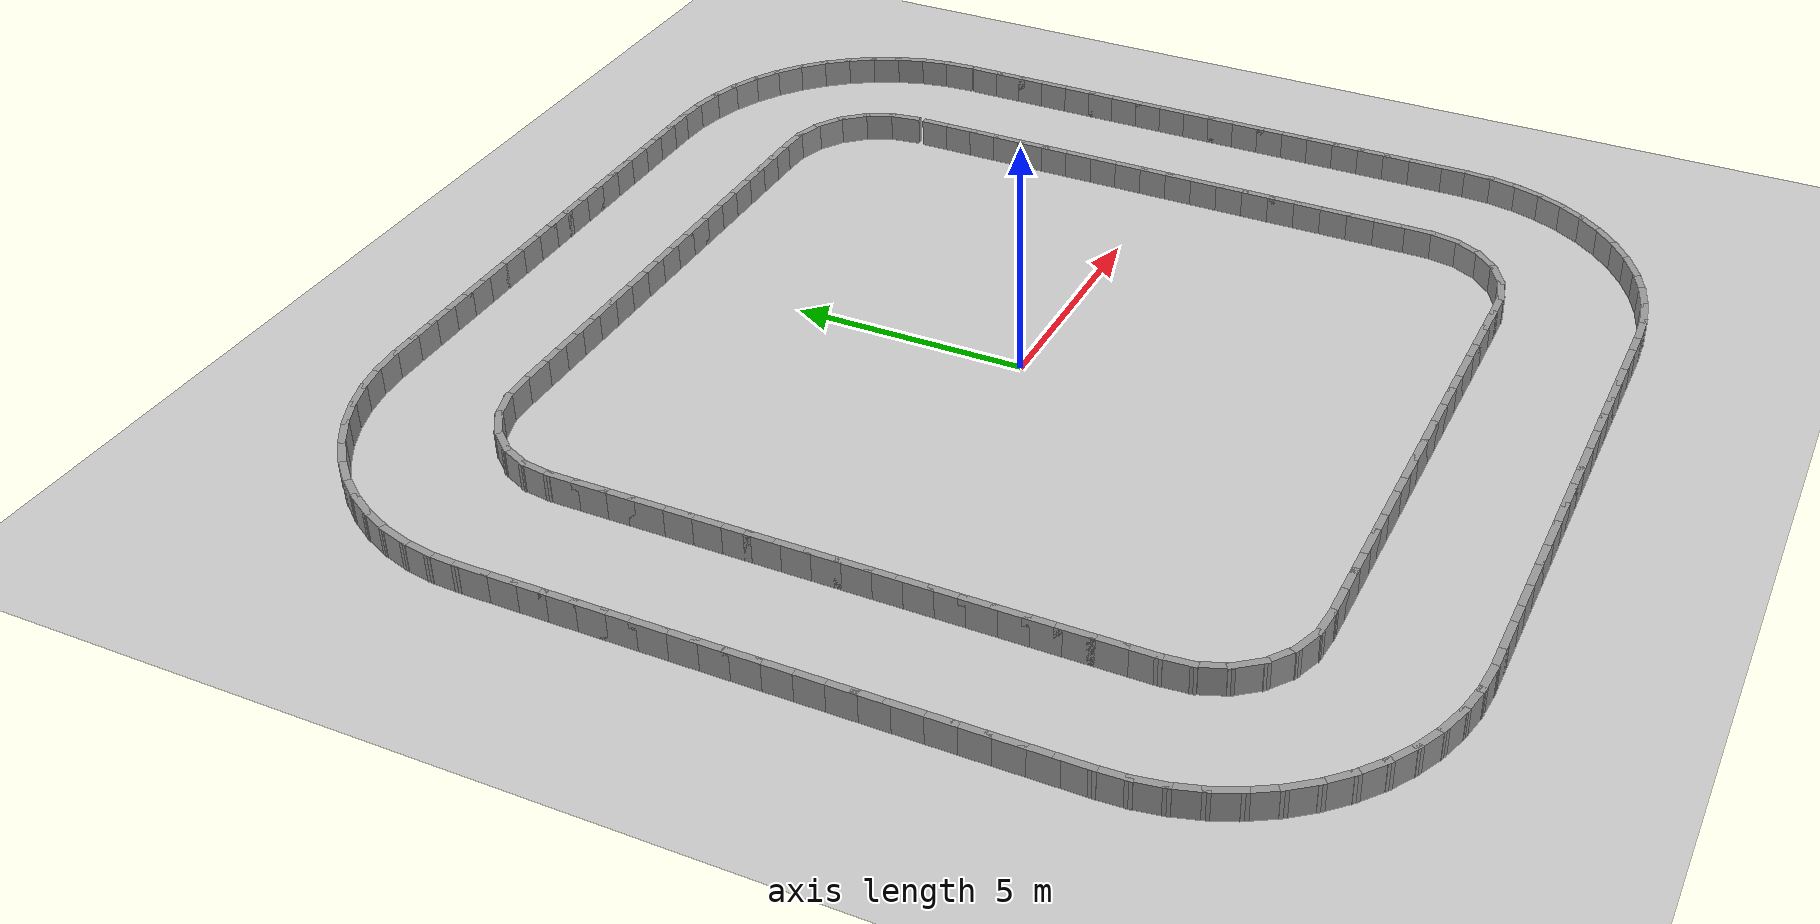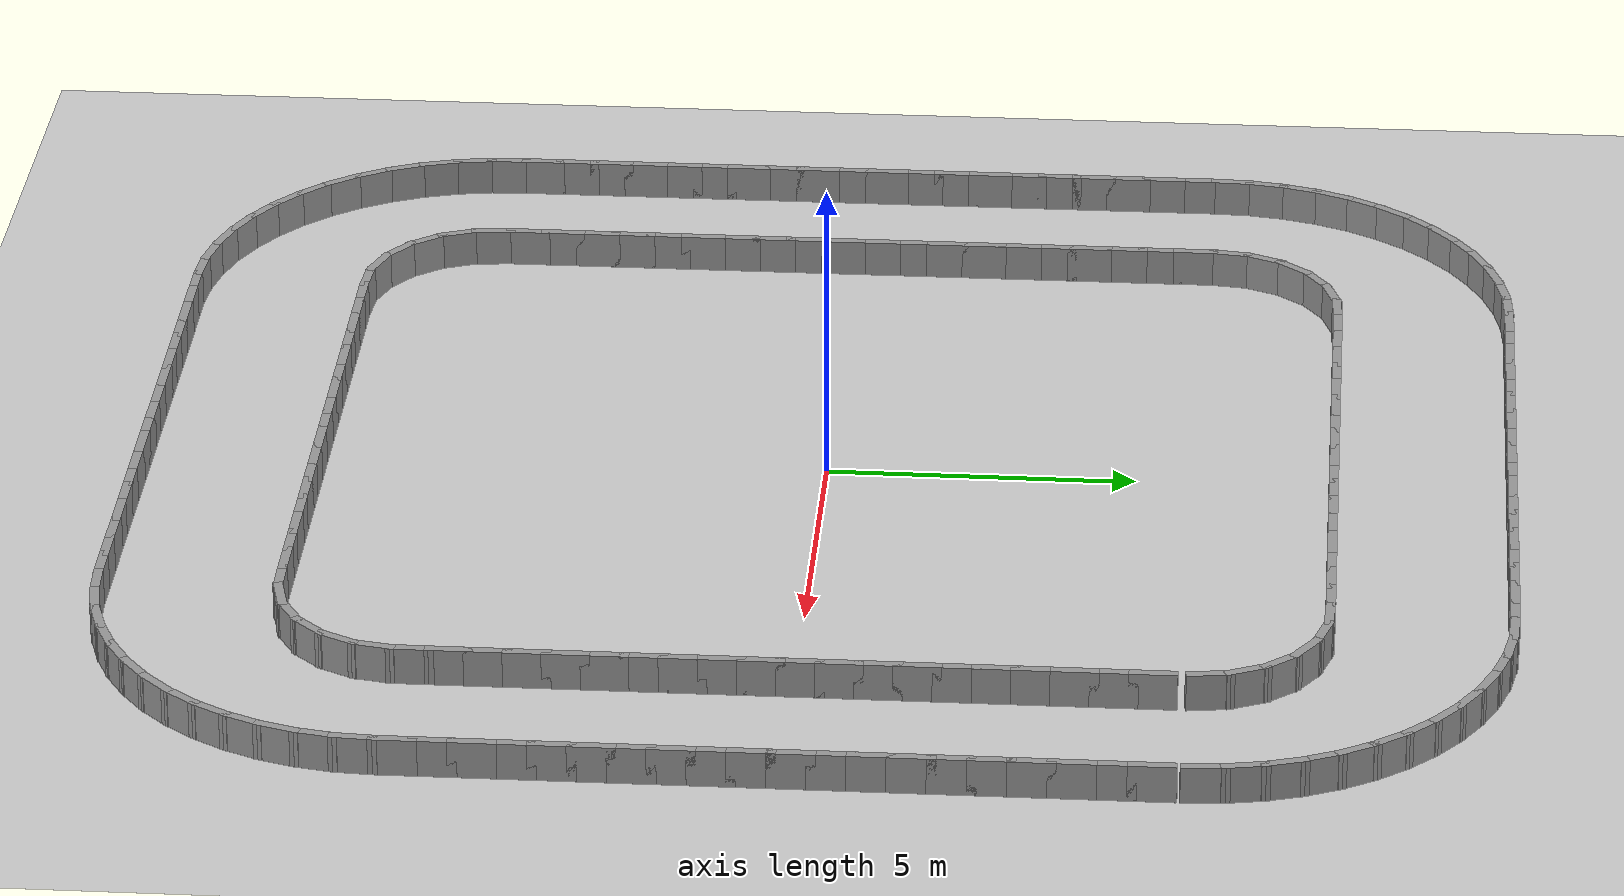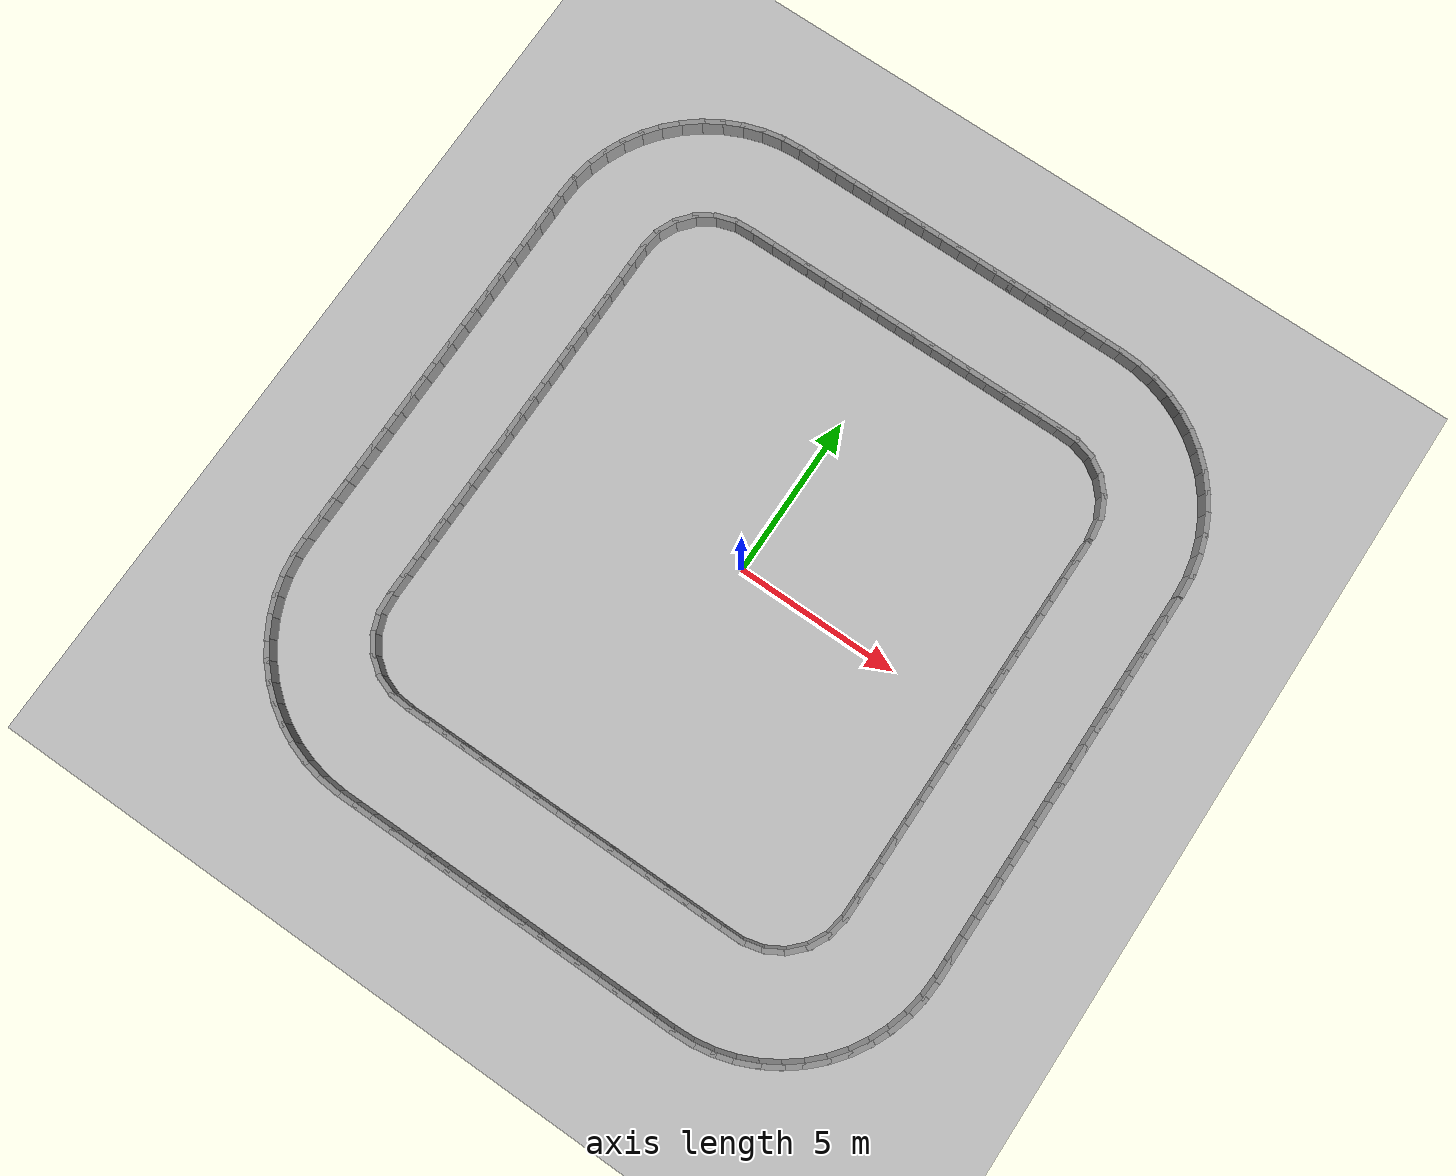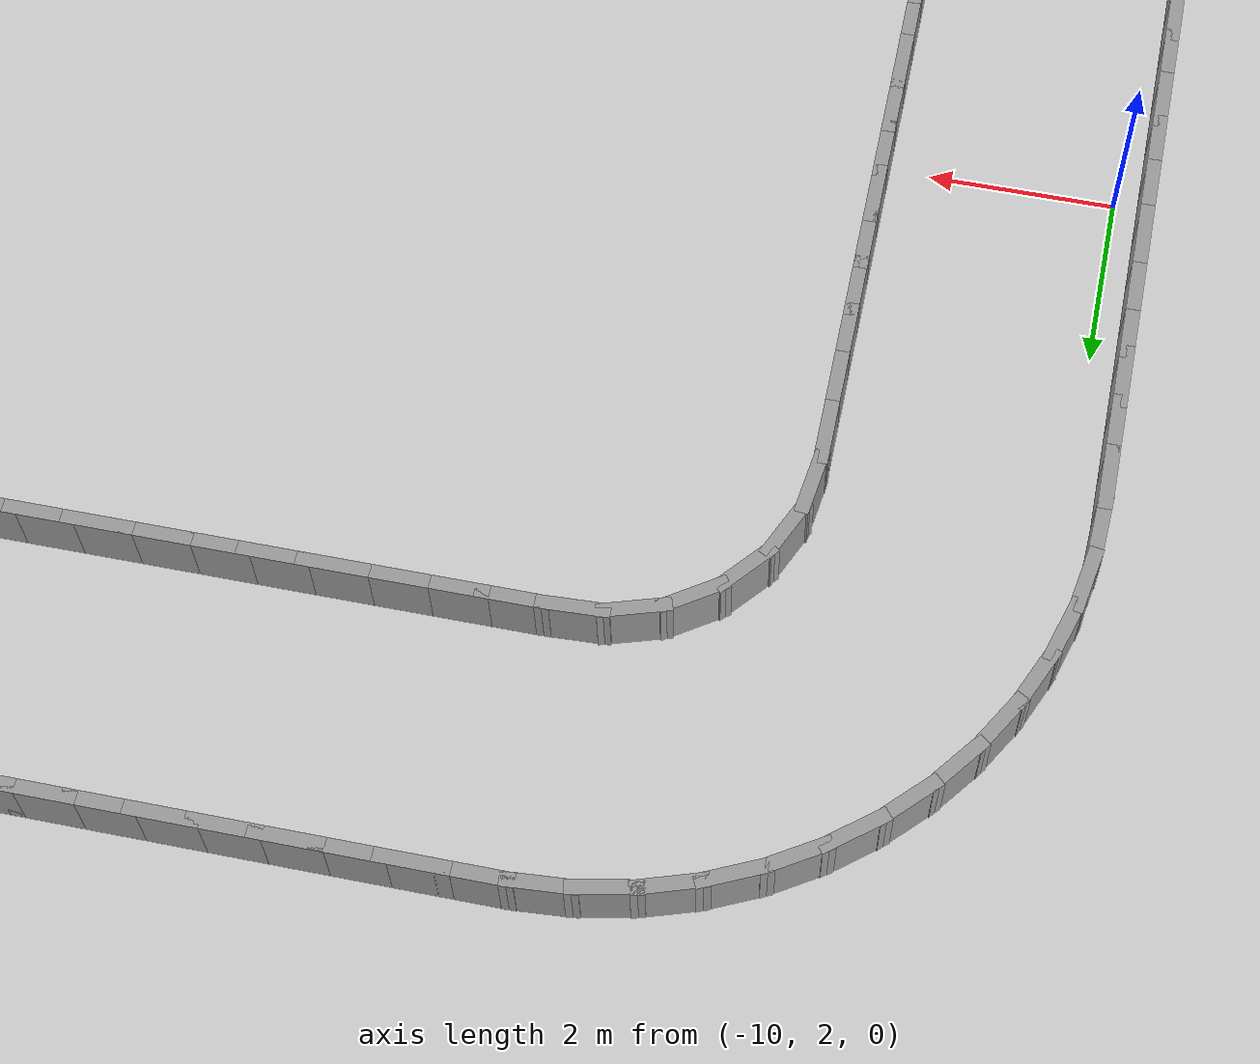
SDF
<?xml version="1.0" ?>
<sdf version='1.7'>
  <world name='default'>
    <plugin name='gazebo_ros_state' filename='libgazebo_ros_state.so'>
      <ros>
        <namespace>/</namespace>
      </ros>
      <update_rate>1000.0</update_rate>
    </plugin>

    <light name='sun' type='directional'>
      <cast_shadows>1</cast_shadows>
      <pose>0 0 10 0 -0 0</pose>
      <diffuse>0.8 0.8 0.8 1</diffuse>
      <specular>0.2 0.2 0.2 1</specular>
      <attenuation>
        <range>1000</range>
        <constant>0.9</constant>
        <linear>0.01</linear>
        <quadratic>0.001</quadratic>
      </attenuation>
      <direction>-0.5 0.1 -0.9</direction>
      <spot>
        <inner_angle>0</inner_angle>
        <outer_angle>0</outer_angle>
        <falloff>0</falloff>
      </spot>
    </light>
    <model name='ground_plane'>
      <static>1</static>
      <link name='link'>
        <collision name='collision'>
          <geometry>
            <plane>
              <normal>0 0 1</normal>
              <size>100 100</size>
            </plane>
          </geometry>
          <surface>
            <friction>
              <ode>
                <mu>100</mu>
                <mu2>50</mu2>
              </ode>
              <torsional>
                <ode/>
              </torsional>
            </friction>
            <contact>
              <ode/>
            </contact>
            <bounce/>
          </surface>
          <max_contacts>10</max_contacts>
        </collision>
        <visual name='visual'>
          <cast_shadows>0</cast_shadows>
          <geometry>
            <plane>
              <normal>0 0 1</normal>
              <size>100 100</size>
            </plane>
          </geometry>
          <material>
            <script>
              <uri>file://media/materials/scripts/gazebo.material</uri>
              <name>Gazebo/Grey</name>
            </script>
          </material>
        </visual>
        <self_collide>0</self_collide>
        <enable_wind>0</enable_wind>
        <kinematic>0</kinematic>
      </link>
    </model>
    <gravity>0 0 -9.8</gravity>
    <magnetic_field>6e-06 2.3e-05 -4.2e-05</magnetic_field>
    <atmosphere type='adiabatic'/>
    <physics type='ode'>
      <max_step_size>0.001</max_step_size>
      <real_time_factor>1</real_time_factor>
      <real_time_update_rate>1000</real_time_update_rate>
    </physics>
    <scene>
      <ambient>0.4 0.4 0.4 1</ambient>
      <background>0.7 0.7 0.7 1</background>
      <shadows>1</shadows>
    </scene>
    <audio>
      <device>default</device>
    </audio>
    <wind/>
    <spherical_coordinates>
      <surface_model>EARTH_WGS84</surface_model>
      <latitude_deg>0</latitude_deg>
      <longitude_deg>0</longitude_deg>
      <elevation>0</elevation>
      <heading_deg>0</heading_deg>
    </spherical_coordinates>
  <model name='rand_rrect_00'>
    <pose>0 0 0 0 -0 0</pose>
    <link name='Wall_0'>
      <collision name='Wall_0_Collision'>
        <geometry><box><size>0.7480 0.1500 0.6000</size></box></geometry>
        <pose>0 0 0.3000 0 -0 0</pose>
      </collision>
      <visual name='Wall_0_Visual'>
        <pose>0 0 0.3000 0 -0 0</pose>
        <geometry><box><size>0.7480 0.1500 0.6000</size></box></geometry>
        <material>
          <script>
            <uri>file://media/materials/scripts/gazebo.material</uri>
            <name>Gazebo/Grey</name>
          </script>
          <ambient>1 1 1 1</ambient>
        </material>
      </visual>
      <pose>7.4411 6.3776 0 0 -0 1.71334</pose>
    </link>
    <link name='Wall_1'>
      <collision name='Wall_1_Collision'>
        <geometry><box><size>0.7480 0.1500 0.6000</size></box></geometry>
        <pose>0 0 0.3000 0 -0 0</pose>
      </collision>
      <visual name='Wall_1_Visual'>
        <pose>0 0 0.3000 0 -0 0</pose>
        <geometry><box><size>0.7480 0.1500 0.6000</size></box></geometry>
        <material>
          <script>
            <uri>file://media/materials/scripts/gazebo.material</uri>
            <name>Gazebo/Grey</name>
          </script>
          <ambient>1 1 1 1</ambient>
        </material>
      </visual>
      <pose>7.2746 6.9457 0 0 -0 1.99840</pose>
    </link>
    <link name='Wall_2'>
      <collision name='Wall_2_Collision'>
        <geometry><box><size>0.7480 0.1500 0.6000</size></box></geometry>
        <pose>0 0 0.3000 0 -0 0</pose>
      </collision>
      <visual name='Wall_2_Visual'>
        <pose>0 0 0.3000 0 -0 0</pose>
        <geometry><box><size>0.7480 0.1500 0.6000</size></box></geometry>
        <material>
          <script>
            <uri>file://media/materials/scripts/gazebo.material</uri>
            <name>Gazebo/Grey</name>
          </script>
          <ambient>1 1 1 1</ambient>
        </material>
      </visual>
      <pose>6.9551 7.4439 0 0 -0 2.28347</pose>
    </link>
    <link name='Wall_3'>
      <collision name='Wall_3_Collision'>
        <geometry><box><size>0.7480 0.1500 0.6000</size></box></geometry>
        <pose>0 0 0.3000 0 -0 0</pose>
      </collision>
      <visual name='Wall_3_Visual'>
        <pose>0 0 0.3000 0 -0 0</pose>
        <geometry><box><size>0.7480 0.1500 0.6000</size></box></geometry>
        <material>
          <script>
            <uri>file://media/materials/scripts/gazebo.material</uri>
            <name>Gazebo/Grey</name>
          </script>
          <ambient>1 1 1 1</ambient>
        </material>
      </visual>
      <pose>6.5084 7.8323 0 0 -0 2.56856</pose>
    </link>
    <link name='Wall_4'>
      <collision name='Wall_4_Collision'>
        <geometry><box><size>0.7480 0.1500 0.6000</size></box></geometry>
        <pose>0 0 0.3000 0 -0 0</pose>
      </collision>
      <visual name='Wall_4_Visual'>
        <pose>0 0 0.3000 0 -0 0</pose>
        <geometry><box><size>0.7480 0.1500 0.6000</size></box></geometry>
        <material>
          <script>
            <uri>file://media/materials/scripts/gazebo.material</uri>
            <name>Gazebo/Grey</name>
          </script>
          <ambient>1 1 1 1</ambient>
        </material>
      </visual>
      <pose>5.9705 8.0793 0 0 -0 2.85362</pose>
    </link>
    <link name='Wall_5'>
      <collision name='Wall_5_Collision'>
        <geometry><box><size>0.7493 0.1500 0.6000</size></box></geometry>
        <pose>0 0 0.3000 0 -0 0</pose>
      </collision>
      <visual name='Wall_5_Visual'>
        <pose>0 0 0.3000 0 -0 0</pose>
        <geometry><box><size>0.7493 0.1500 0.6000</size></box></geometry>
        <material>
          <script>
            <uri>file://media/materials/scripts/gazebo.material</uri>
            <name>Gazebo/Grey</name>
          </script>
          <ambient>1 1 1 1</ambient>
        </material>
      </visual>
      <pose>5.3844 8.1753 0 0 -0 3.10450</pose>
    </link>
    <link name='Wall_6'>
      <collision name='Wall_6_Collision'>
        <geometry><box><size>0.7500 0.1500 0.6000</size></box></geometry>
        <pose>0 0 0.3000 0 -0 0</pose>
      </collision>
      <visual name='Wall_6_Visual'>
        <pose>0 0 0.3000 0 -0 0</pose>
        <geometry><box><size>0.7500 0.1500 0.6000</size></box></geometry>
        <material>
          <script>
            <uri>file://media/materials/scripts/gazebo.material</uri>
            <name>Gazebo/Grey</name>
          </script>
          <ambient>1 1 1 1</ambient>
        </material>
      </visual>
      <pose>4.7849 8.1864 0 0 -0 3.14159</pose>
    </link>
    <link name='Wall_7'>
      <collision name='Wall_7_Collision'>
        <geometry><box><size>0.7500 0.1500 0.6000</size></box></geometry>
        <pose>0 0 0.3000 0 -0 0</pose>
      </collision>
      <visual name='Wall_7_Visual'>
        <pose>0 0 0.3000 0 -0 0</pose>
        <geometry><box><size>0.7500 0.1500 0.6000</size></box></geometry>
        <material>
          <script>
            <uri>file://media/materials/scripts/gazebo.material</uri>
            <name>Gazebo/Grey</name>
          </script>
          <ambient>1 1 1 1</ambient>
        </material>
      </visual>
      <pose>4.1849 8.1864 0 0 -0 3.14159</pose>
    </link>
    <link name='Wall_8'>
      <collision name='Wall_8_Collision'>
        <geometry><box><size>0.7500 0.1500 0.6000</size></box></geometry>
        <pose>0 0 0.3000 0 -0 0</pose>
      </collision>
      <visual name='Wall_8_Visual'>
        <pose>0 0 0.3000 0 -0 0</pose>
        <geometry><box><size>0.7500 0.1500 0.6000</size></box></geometry>
        <material>
          <script>
            <uri>file://media/materials/scripts/gazebo.material</uri>
            <name>Gazebo/Grey</name>
          </script>
          <ambient>1 1 1 1</ambient>
        </material>
      </visual>
      <pose>3.5849 8.1864 0 0 -0 3.14159</pose>
    </link>
    <link name='Wall_9'>
      <collision name='Wall_9_Collision'>
        <geometry><box><size>0.7500 0.1500 0.6000</size></box></geometry>
        <pose>0 0 0.3000 0 -0 0</pose>
      </collision>
      <visual name='Wall_9_Visual'>
        <pose>0 0 0.3000 0 -0 0</pose>
        <geometry><box><size>0.7500 0.1500 0.6000</size></box></geometry>
        <material>
          <script>
            <uri>file://media/materials/scripts/gazebo.material</uri>
            <name>Gazebo/Grey</name>
          </script>
          <ambient>1 1 1 1</ambient>
        </material>
      </visual>
      <pose>2.9849 8.1864 0 0 -0 3.14159</pose>
    </link>
    <link name='Wall_10'>
      <collision name='Wall_10_Collision'>
        <geometry><box><size>0.7500 0.1500 0.6000</size></box></geometry>
        <pose>0 0 0.3000 0 -0 0</pose>
      </collision>
      <visual name='Wall_10_Visual'>
        <pose>0 0 0.3000 0 -0 0</pose>
        <geometry><box><size>0.7500 0.1500 0.6000</size></box></geometry>
        <material>
          <script>
            <uri>file://media/materials/scripts/gazebo.material</uri>
            <name>Gazebo/Grey</name>
          </script>
          <ambient>1 1 1 1</ambient>
        </material>
      </visual>
      <pose>2.3849 8.1864 0 0 -0 3.14159</pose>
    </link>
    <link name='Wall_11'>
      <collision name='Wall_11_Collision'>
        <geometry><box><size>0.7500 0.1500 0.6000</size></box></geometry>
        <pose>0 0 0.3000 0 -0 0</pose>
      </collision>
      <visual name='Wall_11_Visual'>
        <pose>0 0 0.3000 0 -0 0</pose>
        <geometry><box><size>0.7500 0.1500 0.6000</size></box></geometry>
        <material>
          <script>
            <uri>file://media/materials/scripts/gazebo.material</uri>
            <name>Gazebo/Grey</name>
          </script>
          <ambient>1 1 1 1</ambient>
        </material>
      </visual>
      <pose>1.7849 8.1864 0 0 -0 3.14159</pose>
    </link>
    <link name='Wall_12'>
      <collision name='Wall_12_Collision'>
        <geometry><box><size>0.7500 0.1500 0.6000</size></box></geometry>
        <pose>0 0 0.3000 0 -0 0</pose>
      </collision>
      <visual name='Wall_12_Visual'>
        <pose>0 0 0.3000 0 -0 0</pose>
        <geometry><box><size>0.7500 0.1500 0.6000</size></box></geometry>
        <material>
          <script>
            <uri>file://media/materials/scripts/gazebo.material</uri>
            <name>Gazebo/Grey</name>
          </script>
          <ambient>1 1 1 1</ambient>
        </material>
      </visual>
      <pose>1.1849 8.1864 0 0 -0 3.14159</pose>
    </link>
    <link name='Wall_13'>
      <collision name='Wall_13_Collision'>
        <geometry><box><size>0.7500 0.1500 0.6000</size></box></geometry>
        <pose>0 0 0.3000 0 -0 0</pose>
      </collision>
      <visual name='Wall_13_Visual'>
        <pose>0 0 0.3000 0 -0 0</pose>
        <geometry><box><size>0.7500 0.1500 0.6000</size></box></geometry>
        <material>
          <script>
            <uri>file://media/materials/scripts/gazebo.material</uri>
            <name>Gazebo/Grey</name>
          </script>
          <ambient>1 1 1 1</ambient>
        </material>
      </visual>
      <pose>0.5849 8.1864 0 0 -0 3.14159</pose>
    </link>
    <link name='Wall_14'>
      <collision name='Wall_14_Collision'>
        <geometry><box><size>0.7500 0.1500 0.6000</size></box></geometry>
        <pose>0 0 0.3000 0 -0 0</pose>
      </collision>
      <visual name='Wall_14_Visual'>
        <pose>0 0 0.3000 0 -0 0</pose>
        <geometry><box><size>0.7500 0.1500 0.6000</size></box></geometry>
        <material>
          <script>
            <uri>file://media/materials/scripts/gazebo.material</uri>
            <name>Gazebo/Grey</name>
          </script>
          <ambient>1 1 1 1</ambient>
        </material>
      </visual>
      <pose>-0.0151 8.1864 0 0 -0 3.14159</pose>
    </link>
    <link name='Wall_15'>
      <collision name='Wall_15_Collision'>
        <geometry><box><size>0.7500 0.1500 0.6000</size></box></geometry>
        <pose>0 0 0.3000 0 -0 0</pose>
      </collision>
      <visual name='Wall_15_Visual'>
        <pose>0 0 0.3000 0 -0 0</pose>
        <geometry><box><size>0.7500 0.1500 0.6000</size></box></geometry>
        <material>
          <script>
            <uri>file://media/materials/scripts/gazebo.material</uri>
            <name>Gazebo/Grey</name>
          </script>
          <ambient>1 1 1 1</ambient>
        </material>
      </visual>
      <pose>-0.6151 8.1864 0 0 -0 3.14159</pose>
    </link>
    <link name='Wall_16'>
      <collision name='Wall_16_Collision'>
        <geometry><box><size>0.7500 0.1500 0.6000</size></box></geometry>
        <pose>0 0 0.3000 0 -0 0</pose>
      </collision>
      <visual name='Wall_16_Visual'>
        <pose>0 0 0.3000 0 -0 0</pose>
        <geometry><box><size>0.7500 0.1500 0.6000</size></box></geometry>
        <material>
          <script>
            <uri>file://media/materials/scripts/gazebo.material</uri>
            <name>Gazebo/Grey</name>
          </script>
          <ambient>1 1 1 1</ambient>
        </material>
      </visual>
      <pose>-1.2151 8.1864 0 0 -0 3.14159</pose>
    </link>
    <link name='Wall_17'>
      <collision name='Wall_17_Collision'>
        <geometry><box><size>0.7500 0.1500 0.6000</size></box></geometry>
        <pose>0 0 0.3000 0 -0 0</pose>
      </collision>
      <visual name='Wall_17_Visual'>
        <pose>0 0 0.3000 0 -0 0</pose>
        <geometry><box><size>0.7500 0.1500 0.6000</size></box></geometry>
        <material>
          <script>
            <uri>file://media/materials/scripts/gazebo.material</uri>
            <name>Gazebo/Grey</name>
          </script>
          <ambient>1 1 1 1</ambient>
        </material>
      </visual>
      <pose>-1.8151 8.1864 0 0 -0 3.14159</pose>
    </link>
    <link name='Wall_18'>
      <collision name='Wall_18_Collision'>
        <geometry><box><size>0.7500 0.1500 0.6000</size></box></geometry>
        <pose>0 0 0.3000 0 -0 0</pose>
      </collision>
      <visual name='Wall_18_Visual'>
        <pose>0 0 0.3000 0 -0 0</pose>
        <geometry><box><size>0.7500 0.1500 0.6000</size></box></geometry>
        <material>
          <script>
            <uri>file://media/materials/scripts/gazebo.material</uri>
            <name>Gazebo/Grey</name>
          </script>
          <ambient>1 1 1 1</ambient>
        </material>
      </visual>
      <pose>-2.4151 8.1864 0 0 -0 3.14159</pose>
    </link>
    <link name='Wall_19'>
      <collision name='Wall_19_Collision'>
        <geometry><box><size>0.7500 0.1500 0.6000</size></box></geometry>
        <pose>0 0 0.3000 0 -0 0</pose>
      </collision>
      <visual name='Wall_19_Visual'>
        <pose>0 0 0.3000 0 -0 0</pose>
        <geometry><box><size>0.7500 0.1500 0.6000</size></box></geometry>
        <material>
          <script>
            <uri>file://media/materials/scripts/gazebo.material</uri>
            <name>Gazebo/Grey</name>
          </script>
          <ambient>1 1 1 1</ambient>
        </material>
      </visual>
      <pose>-3.0151 8.1864 0 0 -0 3.14159</pose>
    </link>
    <link name='Wall_20'>
      <collision name='Wall_20_Collision'>
        <geometry><box><size>0.7500 0.1500 0.6000</size></box></geometry>
        <pose>0 0 0.3000 0 -0 0</pose>
      </collision>
      <visual name='Wall_20_Visual'>
        <pose>0 0 0.3000 0 -0 0</pose>
        <geometry><box><size>0.7500 0.1500 0.6000</size></box></geometry>
        <material>
          <script>
            <uri>file://media/materials/scripts/gazebo.material</uri>
            <name>Gazebo/Grey</name>
          </script>
          <ambient>1 1 1 1</ambient>
        </material>
      </visual>
      <pose>-3.6151 8.1864 0 0 -0 3.14159</pose>
    </link>
    <link name='Wall_21'>
      <collision name='Wall_21_Collision'>
        <geometry><box><size>0.7500 0.1500 0.6000</size></box></geometry>
        <pose>0 0 0.3000 0 -0 0</pose>
      </collision>
      <visual name='Wall_21_Visual'>
        <pose>0 0 0.3000 0 -0 0</pose>
        <geometry><box><size>0.7500 0.1500 0.6000</size></box></geometry>
        <material>
          <script>
            <uri>file://media/materials/scripts/gazebo.material</uri>
            <name>Gazebo/Grey</name>
          </script>
          <ambient>1 1 1 1</ambient>
        </material>
      </visual>
      <pose>-4.2151 8.1864 0 0 -0 3.14159</pose>
    </link>
    <link name='Wall_22'>
      <collision name='Wall_22_Collision'>
        <geometry><box><size>0.7500 0.1500 0.6000</size></box></geometry>
        <pose>0 0 0.3000 0 -0 0</pose>
      </collision>
      <visual name='Wall_22_Visual'>
        <pose>0 0 0.3000 0 -0 0</pose>
        <geometry><box><size>0.7500 0.1500 0.6000</size></box></geometry>
        <material>
          <script>
            <uri>file://media/materials/scripts/gazebo.material</uri>
            <name>Gazebo/Grey</name>
          </script>
          <ambient>1 1 1 1</ambient>
        </material>
      </visual>
      <pose>-4.8151 8.1864 0 0 -0 3.14159</pose>
    </link>
    <link name='Wall_23'>
      <collision name='Wall_23_Collision'>
        <geometry><box><size>0.7492 0.1500 0.6000</size></box></geometry>
        <pose>0 0 0.3000 0 -0 0</pose>
      </collision>
      <visual name='Wall_23_Visual'>
        <pose>0 0 0.3000 0 -0 0</pose>
        <geometry><box><size>0.7492 0.1500 0.6000</size></box></geometry>
        <material>
          <script>
            <uri>file://media/materials/scripts/gazebo.material</uri>
            <name>Gazebo/Grey</name>
          </script>
          <ambient>1 1 1 1</ambient>
        </material>
      </visual>
      <pose>-5.4144 8.1730 0 0 -0 -3.09682</pose>
    </link>
    <link name='Wall_24'>
      <collision name='Wall_24_Collision'>
        <geometry><box><size>0.7480 0.1500 0.6000</size></box></geometry>
        <pose>0 0 0.3000 0 -0 0</pose>
      </collision>
      <visual name='Wall_24_Visual'>
        <pose>0 0 0.3000 0 -0 0</pose>
        <geometry><box><size>0.7480 0.1500 0.6000</size></box></geometry>
        <material>
          <script>
            <uri>file://media/materials/scripts/gazebo.material</uri>
            <name>Gazebo/Grey</name>
          </script>
          <ambient>1 1 1 1</ambient>
        </material>
      </visual>
      <pose>-5.9991 8.0706 0 0 -0 -2.83928</pose>
    </link>
    <link name='Wall_25'>
      <collision name='Wall_25_Collision'>
        <geometry><box><size>0.7480 0.1500 0.6000</size></box></geometry>
        <pose>0 0 0.3000 0 -0 0</pose>
      </collision>
      <visual name='Wall_25_Visual'>
        <pose>0 0 0.3000 0 -0 0</pose>
        <geometry><box><size>0.7480 0.1500 0.6000</size></box></geometry>
        <material>
          <script>
            <uri>file://media/materials/scripts/gazebo.material</uri>
            <name>Gazebo/Grey</name>
          </script>
          <ambient>1 1 1 1</ambient>
        </material>
      </visual>
      <pose>-6.5334 7.8159 0 0 -0 -2.55420</pose>
    </link>
    <link name='Wall_26'>
      <collision name='Wall_26_Collision'>
        <geometry><box><size>0.7480 0.1500 0.6000</size></box></geometry>
        <pose>0 0 0.3000 0 -0 0</pose>
      </collision>
      <visual name='Wall_26_Visual'>
        <pose>0 0 0.3000 0 -0 0</pose>
        <geometry><box><size>0.7480 0.1500 0.6000</size></box></geometry>
        <material>
          <script>
            <uri>file://media/materials/scripts/gazebo.material</uri>
            <name>Gazebo/Grey</name>
          </script>
          <ambient>1 1 1 1</ambient>
        </material>
      </visual>
      <pose>-6.9745 7.4212 0 0 -0 -2.26912</pose>
    </link>
    <link name='Wall_27'>
      <collision name='Wall_27_Collision'>
        <geometry><box><size>0.7480 0.1500 0.6000</size></box></geometry>
        <pose>0 0 0.3000 0 -0 0</pose>
      </collision>
      <visual name='Wall_27_Visual'>
        <pose>0 0 0.3000 0 -0 0</pose>
        <geometry><box><size>0.7480 0.1500 0.6000</size></box></geometry>
        <material>
          <script>
            <uri>file://media/materials/scripts/gazebo.material</uri>
            <name>Gazebo/Grey</name>
          </script>
          <ambient>1 1 1 1</ambient>
        </material>
      </visual>
      <pose>-7.2868 6.9184 0 0 -0 -1.98406</pose>
    </link>
    <link name='Wall_28'>
      <collision name='Wall_28_Collision'>
        <geometry><box><size>0.7480 0.1500 0.6000</size></box></geometry>
        <pose>0 0 0.3000 0 -0 0</pose>
      </collision>
      <visual name='Wall_28_Visual'>
        <pose>0 0 0.3000 0 -0 0</pose>
        <geometry><box><size>0.7480 0.1500 0.6000</size></box></geometry>
        <material>
          <script>
            <uri>file://media/materials/scripts/gazebo.material</uri>
            <name>Gazebo/Grey</name>
          </script>
          <ambient>1 1 1 1</ambient>
        </material>
      </visual>
      <pose>-7.4452 6.3480 0 0 -0 -1.69935</pose>
    </link>
    <link name='Wall_29'>
      <collision name='Wall_29_Collision'>
        <geometry><box><size>0.7500 0.1500 0.6000</size></box></geometry>
        <pose>0 0 0.3000 0 -0 0</pose>
      </collision>
      <visual name='Wall_29_Visual'>
        <pose>0 0 0.3000 0 -0 0</pose>
        <geometry><box><size>0.7500 0.1500 0.6000</size></box></geometry>
        <material>
          <script>
            <uri>file://media/materials/scripts/gazebo.material</uri>
            <name>Gazebo/Grey</name>
          </script>
          <ambient>1 1 1 1</ambient>
        </material>
      </visual>
      <pose>-7.4835 5.7515 0 0 -0 -1.57080</pose>
    </link>
    <link name='Wall_30'>
      <collision name='Wall_30_Collision'>
        <geometry><box><size>0.7500 0.1500 0.6000</size></box></geometry>
        <pose>0 0 0.3000 0 -0 0</pose>
      </collision>
      <visual name='Wall_30_Visual'>
        <pose>0 0 0.3000 0 -0 0</pose>
        <geometry><box><size>0.7500 0.1500 0.6000</size></box></geometry>
        <material>
          <script>
            <uri>file://media/materials/scripts/gazebo.material</uri>
            <name>Gazebo/Grey</name>
          </script>
          <ambient>1 1 1 1</ambient>
        </material>
      </visual>
      <pose>-7.4835 5.1515 0 0 -0 -1.57080</pose>
    </link>
    <link name='Wall_31'>
      <collision name='Wall_31_Collision'>
        <geometry><box><size>0.7500 0.1500 0.6000</size></box></geometry>
        <pose>0 0 0.3000 0 -0 0</pose>
      </collision>
      <visual name='Wall_31_Visual'>
        <pose>0 0 0.3000 0 -0 0</pose>
        <geometry><box><size>0.7500 0.1500 0.6000</size></box></geometry>
        <material>
          <script>
            <uri>file://media/materials/scripts/gazebo.material</uri>
            <name>Gazebo/Grey</name>
          </script>
          <ambient>1 1 1 1</ambient>
        </material>
      </visual>
      <pose>-7.4835 4.5515 0 0 -0 -1.57080</pose>
    </link>
    <link name='Wall_32'>
      <collision name='Wall_32_Collision'>
        <geometry><box><size>0.7500 0.1500 0.6000</size></box></geometry>
        <pose>0 0 0.3000 0 -0 0</pose>
      </collision>
      <visual name='Wall_32_Visual'>
        <pose>0 0 0.3000 0 -0 0</pose>
        <geometry><box><size>0.7500 0.1500 0.6000</size></box></geometry>
        <material>
          <script>
            <uri>file://media/materials/scripts/gazebo.material</uri>
            <name>Gazebo/Grey</name>
          </script>
          <ambient>1 1 1 1</ambient>
        </material>
      </visual>
      <pose>-7.4835 3.9515 0 0 -0 -1.57080</pose>
    </link>
    <link name='Wall_33'>
      <collision name='Wall_33_Collision'>
        <geometry><box><size>0.7500 0.1500 0.6000</size></box></geometry>
        <pose>0 0 0.3000 0 -0 0</pose>
      </collision>
      <visual name='Wall_33_Visual'>
        <pose>0 0 0.3000 0 -0 0</pose>
        <geometry><box><size>0.7500 0.1500 0.6000</size></box></geometry>
        <material>
          <script>
            <uri>file://media/materials/scripts/gazebo.material</uri>
            <name>Gazebo/Grey</name>
          </script>
          <ambient>1 1 1 1</ambient>
        </material>
      </visual>
      <pose>-7.4835 3.3515 0 0 -0 -1.57080</pose>
    </link>
    <link name='Wall_34'>
      <collision name='Wall_34_Collision'>
        <geometry><box><size>0.7500 0.1500 0.6000</size></box></geometry>
        <pose>0 0 0.3000 0 -0 0</pose>
      </collision>
      <visual name='Wall_34_Visual'>
        <pose>0 0 0.3000 0 -0 0</pose>
        <geometry><box><size>0.7500 0.1500 0.6000</size></box></geometry>
        <material>
          <script>
            <uri>file://media/materials/scripts/gazebo.material</uri>
            <name>Gazebo/Grey</name>
          </script>
          <ambient>1 1 1 1</ambient>
        </material>
      </visual>
      <pose>-7.4835 2.7515 0 0 -0 -1.57080</pose>
    </link>
    <link name='Wall_35'>
      <collision name='Wall_35_Collision'>
        <geometry><box><size>0.7500 0.1500 0.6000</size></box></geometry>
        <pose>0 0 0.3000 0 -0 0</pose>
      </collision>
      <visual name='Wall_35_Visual'>
        <pose>0 0 0.3000 0 -0 0</pose>
        <geometry><box><size>0.7500 0.1500 0.6000</size></box></geometry>
        <material>
          <script>
            <uri>file://media/materials/scripts/gazebo.material</uri>
            <name>Gazebo/Grey</name>
          </script>
          <ambient>1 1 1 1</ambient>
        </material>
      </visual>
      <pose>-7.4835 2.1515 0 0 -0 -1.57080</pose>
    </link>
    <link name='Wall_36'>
      <collision name='Wall_36_Collision'>
        <geometry><box><size>0.7500 0.1500 0.6000</size></box></geometry>
        <pose>0 0 0.3000 0 -0 0</pose>
      </collision>
      <visual name='Wall_36_Visual'>
        <pose>0 0 0.3000 0 -0 0</pose>
        <geometry><box><size>0.7500 0.1500 0.6000</size></box></geometry>
        <material>
          <script>
            <uri>file://media/materials/scripts/gazebo.material</uri>
            <name>Gazebo/Grey</name>
          </script>
          <ambient>1 1 1 1</ambient>
        </material>
      </visual>
      <pose>-7.4835 1.5515 0 0 -0 -1.57080</pose>
    </link>
    <link name='Wall_37'>
      <collision name='Wall_37_Collision'>
        <geometry><box><size>0.7500 0.1500 0.6000</size></box></geometry>
        <pose>0 0 0.3000 0 -0 0</pose>
      </collision>
      <visual name='Wall_37_Visual'>
        <pose>0 0 0.3000 0 -0 0</pose>
        <geometry><box><size>0.7500 0.1500 0.6000</size></box></geometry>
        <material>
          <script>
            <uri>file://media/materials/scripts/gazebo.material</uri>
            <name>Gazebo/Grey</name>
          </script>
          <ambient>1 1 1 1</ambient>
        </material>
      </visual>
      <pose>-7.4835 0.9515 0 0 -0 -1.57080</pose>
    </link>
    <link name='Wall_38'>
      <collision name='Wall_38_Collision'>
        <geometry><box><size>0.7500 0.1500 0.6000</size></box></geometry>
        <pose>0 0 0.3000 0 -0 0</pose>
      </collision>
      <visual name='Wall_38_Visual'>
        <pose>0 0 0.3000 0 -0 0</pose>
        <geometry><box><size>0.7500 0.1500 0.6000</size></box></geometry>
        <material>
          <script>
            <uri>file://media/materials/scripts/gazebo.material</uri>
            <name>Gazebo/Grey</name>
          </script>
          <ambient>1 1 1 1</ambient>
        </material>
      </visual>
      <pose>-7.4835 0.3515 0 0 -0 -1.57080</pose>
    </link>
    <link name='Wall_39'>
      <collision name='Wall_39_Collision'>
        <geometry><box><size>0.7500 0.1500 0.6000</size></box></geometry>
        <pose>0 0 0.3000 0 -0 0</pose>
      </collision>
      <visual name='Wall_39_Visual'>
        <pose>0 0 0.3000 0 -0 0</pose>
        <geometry><box><size>0.7500 0.1500 0.6000</size></box></geometry>
        <material>
          <script>
            <uri>file://media/materials/scripts/gazebo.material</uri>
            <name>Gazebo/Grey</name>
          </script>
          <ambient>1 1 1 1</ambient>
        </material>
      </visual>
      <pose>-7.4835 -0.2485 0 0 -0 -1.57080</pose>
    </link>
    <link name='Wall_40'>
      <collision name='Wall_40_Collision'>
        <geometry><box><size>0.7500 0.1500 0.6000</size></box></geometry>
        <pose>0 0 0.3000 0 -0 0</pose>
      </collision>
      <visual name='Wall_40_Visual'>
        <pose>0 0 0.3000 0 -0 0</pose>
        <geometry><box><size>0.7500 0.1500 0.6000</size></box></geometry>
        <material>
          <script>
            <uri>file://media/materials/scripts/gazebo.material</uri>
            <name>Gazebo/Grey</name>
          </script>
          <ambient>1 1 1 1</ambient>
        </material>
      </visual>
      <pose>-7.4835 -0.8485 0 0 -0 -1.57080</pose>
    </link>
    <link name='Wall_41'>
      <collision name='Wall_41_Collision'>
        <geometry><box><size>0.7500 0.1500 0.6000</size></box></geometry>
        <pose>0 0 0.3000 0 -0 0</pose>
      </collision>
      <visual name='Wall_41_Visual'>
        <pose>0 0 0.3000 0 -0 0</pose>
        <geometry><box><size>0.7500 0.1500 0.6000</size></box></geometry>
        <material>
          <script>
            <uri>file://media/materials/scripts/gazebo.material</uri>
            <name>Gazebo/Grey</name>
          </script>
          <ambient>1 1 1 1</ambient>
        </material>
      </visual>
      <pose>-7.4835 -1.4485 0 0 -0 -1.57080</pose>
    </link>
    <link name='Wall_42'>
      <collision name='Wall_42_Collision'>
        <geometry><box><size>0.7500 0.1500 0.6000</size></box></geometry>
        <pose>0 0 0.3000 0 -0 0</pose>
      </collision>
      <visual name='Wall_42_Visual'>
        <pose>0 0 0.3000 0 -0 0</pose>
        <geometry><box><size>0.7500 0.1500 0.6000</size></box></geometry>
        <material>
          <script>
            <uri>file://media/materials/scripts/gazebo.material</uri>
            <name>Gazebo/Grey</name>
          </script>
          <ambient>1 1 1 1</ambient>
        </material>
      </visual>
      <pose>-7.4835 -2.0485 0 0 -0 -1.57080</pose>
    </link>
    <link name='Wall_43'>
      <collision name='Wall_43_Collision'>
        <geometry><box><size>0.7500 0.1500 0.6000</size></box></geometry>
        <pose>0 0 0.3000 0 -0 0</pose>
      </collision>
      <visual name='Wall_43_Visual'>
        <pose>0 0 0.3000 0 -0 0</pose>
        <geometry><box><size>0.7500 0.1500 0.6000</size></box></geometry>
        <material>
          <script>
            <uri>file://media/materials/scripts/gazebo.material</uri>
            <name>Gazebo/Grey</name>
          </script>
          <ambient>1 1 1 1</ambient>
        </material>
      </visual>
      <pose>-7.4835 -2.6485 0 0 -0 -1.57080</pose>
    </link>
    <link name='Wall_44'>
      <collision name='Wall_44_Collision'>
        <geometry><box><size>0.7500 0.1500 0.6000</size></box></geometry>
        <pose>0 0 0.3000 0 -0 0</pose>
      </collision>
      <visual name='Wall_44_Visual'>
        <pose>0 0 0.3000 0 -0 0</pose>
        <geometry><box><size>0.7500 0.1500 0.6000</size></box></geometry>
        <material>
          <script>
            <uri>file://media/materials/scripts/gazebo.material</uri>
            <name>Gazebo/Grey</name>
          </script>
          <ambient>1 1 1 1</ambient>
        </material>
      </visual>
      <pose>-7.4835 -3.2485 0 0 -0 -1.57080</pose>
    </link>
    <link name='Wall_45'>
      <collision name='Wall_45_Collision'>
        <geometry><box><size>0.7500 0.1500 0.6000</size></box></geometry>
        <pose>0 0 0.3000 0 -0 0</pose>
      </collision>
      <visual name='Wall_45_Visual'>
        <pose>0 0 0.3000 0 -0 0</pose>
        <geometry><box><size>0.7500 0.1500 0.6000</size></box></geometry>
        <material>
          <script>
            <uri>file://media/materials/scripts/gazebo.material</uri>
            <name>Gazebo/Grey</name>
          </script>
          <ambient>1 1 1 1</ambient>
        </material>
      </visual>
      <pose>-7.4835 -3.8485 0 0 -0 -1.57080</pose>
    </link>
    <link name='Wall_46'>
      <collision name='Wall_46_Collision'>
        <geometry><box><size>0.7500 0.1500 0.6000</size></box></geometry>
        <pose>0 0 0.3000 0 -0 0</pose>
      </collision>
      <visual name='Wall_46_Visual'>
        <pose>0 0 0.3000 0 -0 0</pose>
        <geometry><box><size>0.7500 0.1500 0.6000</size></box></geometry>
        <material>
          <script>
            <uri>file://media/materials/scripts/gazebo.material</uri>
            <name>Gazebo/Grey</name>
          </script>
          <ambient>1 1 1 1</ambient>
        </material>
      </visual>
      <pose>-7.4835 -4.4485 0 0 -0 -1.57080</pose>
    </link>
    <link name='Wall_47'>
      <collision name='Wall_47_Collision'>
        <geometry><box><size>0.7500 0.1500 0.6000</size></box></geometry>
        <pose>0 0 0.3000 0 -0 0</pose>
      </collision>
      <visual name='Wall_47_Visual'>
        <pose>0 0 0.3000 0 -0 0</pose>
        <geometry><box><size>0.7500 0.1500 0.6000</size></box></geometry>
        <material>
          <script>
            <uri>file://media/materials/scripts/gazebo.material</uri>
            <name>Gazebo/Grey</name>
          </script>
          <ambient>1 1 1 1</ambient>
        </material>
      </visual>
      <pose>-7.4835 -5.0485 0 0 -0 -1.57080</pose>
    </link>
    <link name='Wall_48'>
      <collision name='Wall_48_Collision'>
        <geometry><box><size>0.7500 0.1500 0.6000</size></box></geometry>
        <pose>0 0 0.3000 0 -0 0</pose>
      </collision>
      <visual name='Wall_48_Visual'>
        <pose>0 0 0.3000 0 -0 0</pose>
        <geometry><box><size>0.7500 0.1500 0.6000</size></box></geometry>
        <material>
          <script>
            <uri>file://media/materials/scripts/gazebo.material</uri>
            <name>Gazebo/Grey</name>
          </script>
          <ambient>1 1 1 1</ambient>
        </material>
      </visual>
      <pose>-7.4835 -5.6485 0 0 -0 -1.57080</pose>
    </link>
    <link name='Wall_49'>
      <collision name='Wall_49_Collision'>
        <geometry><box><size>0.7484 0.1500 0.6000</size></box></geometry>
        <pose>0 0 0.3000 0 -0 0</pose>
      </collision>
      <visual name='Wall_49_Visual'>
        <pose>0 0 0.3000 0 -0 0</pose>
        <geometry><box><size>0.7484 0.1500 0.6000</size></box></geometry>
        <material>
          <script>
            <uri>file://media/materials/scripts/gazebo.material</uri>
            <name>Gazebo/Grey</name>
          </script>
          <ambient>1 1 1 1</ambient>
        </material>
      </visual>
      <pose>-7.4577 -6.2466 0 0 -0 -1.48453</pose>
    </link>
    <link name='Wall_50'>
      <collision name='Wall_50_Collision'>
        <geometry><box><size>0.7480 0.1500 0.6000</size></box></geometry>
        <pose>0 0 0.3000 0 -0 0</pose>
      </collision>
      <visual name='Wall_50_Visual'>
        <pose>0 0 0.3000 0 -0 0</pose>
        <geometry><box><size>0.7480 0.1500 0.6000</size></box></geometry>
        <material>
          <script>
            <uri>file://media/materials/scripts/gazebo.material</uri>
            <name>Gazebo/Grey</name>
          </script>
          <ambient>1 1 1 1</ambient>
        </material>
      </visual>
      <pose>-7.3254 -6.8240 0 0 -0 -1.20647</pose>
    </link>
    <link name='Wall_51'>
      <collision name='Wall_51_Collision'>
        <geometry><box><size>0.7480 0.1500 0.6000</size></box></geometry>
        <pose>0 0 0.3000 0 -0 0</pose>
      </collision>
      <visual name='Wall_51_Visual'>
        <pose>0 0 0.3000 0 -0 0</pose>
        <geometry><box><size>0.7480 0.1500 0.6000</size></box></geometry>
        <material>
          <script>
            <uri>file://media/materials/scripts/gazebo.material</uri>
            <name>Gazebo/Grey</name>
          </script>
          <ambient>1 1 1 1</ambient>
        </material>
      </visual>
      <pose>-7.0381 -7.3415 0 0 -0 -0.92140</pose>
    </link>
    <link name='Wall_52'>
      <collision name='Wall_52_Collision'>
        <geometry><box><size>0.7480 0.1500 0.6000</size></box></geometry>
        <pose>0 0 0.3000 0 -0 0</pose>
      </collision>
      <visual name='Wall_52_Visual'>
        <pose>0 0 0.3000 0 -0 0</pose>
        <geometry><box><size>0.7480 0.1500 0.6000</size></box></geometry>
        <material>
          <script>
            <uri>file://media/materials/scripts/gazebo.material</uri>
            <name>Gazebo/Grey</name>
          </script>
          <ambient>1 1 1 1</ambient>
        </material>
      </visual>
      <pose>-6.6168 -7.7573 0 0 -0 -0.63632</pose>
    </link>
    <link name='Wall_53'>
      <collision name='Wall_53_Collision'>
        <geometry><box><size>0.7480 0.1500 0.6000</size></box></geometry>
        <pose>0 0 0.3000 0 -0 0</pose>
      </collision>
      <visual name='Wall_53_Visual'>
        <pose>0 0 0.3000 0 -0 0</pose>
        <geometry><box><size>0.7480 0.1500 0.6000</size></box></geometry>
        <material>
          <script>
            <uri>file://media/materials/scripts/gazebo.material</uri>
            <name>Gazebo/Grey</name>
          </script>
          <ambient>1 1 1 1</ambient>
        </material>
      </visual>
      <pose>-6.0956 -8.0379 0 0 -0 -0.35125</pose>
    </link>
    <link name='Wall_54'>
      <collision name='Wall_54_Collision'>
        <geometry><box><size>0.7486 0.1500 0.6000</size></box></geometry>
        <pose>0 0 0.3000 0 -0 0</pose>
      </collision>
      <visual name='Wall_54_Visual'>
        <pose>0 0 0.3000 0 -0 0</pose>
        <geometry><box><size>0.7486 0.1500 0.6000</size></box></geometry>
        <material>
          <script>
            <uri>file://media/materials/scripts/gazebo.material</uri>
            <name>Gazebo/Grey</name>
          </script>
          <ambient>1 1 1 1</ambient>
        </material>
      </visual>
      <pose>-5.5165 -8.1636 0 0 -0 -0.07639</pose>
    </link>
    <link name='Wall_55'>
      <collision name='Wall_55_Collision'>
        <geometry><box><size>0.7500 0.1500 0.6000</size></box></geometry>
        <pose>0 0 0.3000 0 -0 0</pose>
      </collision>
      <visual name='Wall_55_Visual'>
        <pose>0 0 0.3000 0 -0 0</pose>
        <geometry><box><size>0.7500 0.1500 0.6000</size></box></geometry>
        <material>
          <script>
            <uri>file://media/materials/scripts/gazebo.material</uri>
            <name>Gazebo/Grey</name>
          </script>
          <ambient>1 1 1 1</ambient>
        </material>
      </visual>
      <pose>-4.9181 -8.1864 0 0 -0 0.00000</pose>
    </link>
    <link name='Wall_56'>
      <collision name='Wall_56_Collision'>
        <geometry><box><size>0.7500 0.1500 0.6000</size></box></geometry>
        <pose>0 0 0.3000 0 -0 0</pose>
      </collision>
      <visual name='Wall_56_Visual'>
        <pose>0 0 0.3000 0 -0 0</pose>
        <geometry><box><size>0.7500 0.1500 0.6000</size></box></geometry>
        <material>
          <script>
            <uri>file://media/materials/scripts/gazebo.material</uri>
            <name>Gazebo/Grey</name>
          </script>
          <ambient>1 1 1 1</ambient>
        </material>
      </visual>
      <pose>-4.3181 -8.1864 0 0 -0 0.00000</pose>
    </link>
    <link name='Wall_57'>
      <collision name='Wall_57_Collision'>
        <geometry><box><size>0.7500 0.1500 0.6000</size></box></geometry>
        <pose>0 0 0.3000 0 -0 0</pose>
      </collision>
      <visual name='Wall_57_Visual'>
        <pose>0 0 0.3000 0 -0 0</pose>
        <geometry><box><size>0.7500 0.1500 0.6000</size></box></geometry>
        <material>
          <script>
            <uri>file://media/materials/scripts/gazebo.material</uri>
            <name>Gazebo/Grey</name>
          </script>
          <ambient>1 1 1 1</ambient>
        </material>
      </visual>
      <pose>-3.7181 -8.1864 0 0 -0 0.00000</pose>
    </link>
    <link name='Wall_58'>
      <collision name='Wall_58_Collision'>
        <geometry><box><size>0.7500 0.1500 0.6000</size></box></geometry>
        <pose>0 0 0.3000 0 -0 0</pose>
      </collision>
      <visual name='Wall_58_Visual'>
        <pose>0 0 0.3000 0 -0 0</pose>
        <geometry><box><size>0.7500 0.1500 0.6000</size></box></geometry>
        <material>
          <script>
            <uri>file://media/materials/scripts/gazebo.material</uri>
            <name>Gazebo/Grey</name>
          </script>
          <ambient>1 1 1 1</ambient>
        </material>
      </visual>
      <pose>-3.1181 -8.1864 0 0 -0 0.00000</pose>
    </link>
    <link name='Wall_59'>
      <collision name='Wall_59_Collision'>
        <geometry><box><size>0.7500 0.1500 0.6000</size></box></geometry>
        <pose>0 0 0.3000 0 -0 0</pose>
      </collision>
      <visual name='Wall_59_Visual'>
        <pose>0 0 0.3000 0 -0 0</pose>
        <geometry><box><size>0.7500 0.1500 0.6000</size></box></geometry>
        <material>
          <script>
            <uri>file://media/materials/scripts/gazebo.material</uri>
            <name>Gazebo/Grey</name>
          </script>
          <ambient>1 1 1 1</ambient>
        </material>
      </visual>
      <pose>-2.5181 -8.1864 0 0 -0 0.00000</pose>
    </link>
    <link name='Wall_60'>
      <collision name='Wall_60_Collision'>
        <geometry><box><size>0.7500 0.1500 0.6000</size></box></geometry>
        <pose>0 0 0.3000 0 -0 0</pose>
      </collision>
      <visual name='Wall_60_Visual'>
        <pose>0 0 0.3000 0 -0 0</pose>
        <geometry><box><size>0.7500 0.1500 0.6000</size></box></geometry>
        <material>
          <script>
            <uri>file://media/materials/scripts/gazebo.material</uri>
            <name>Gazebo/Grey</name>
          </script>
          <ambient>1 1 1 1</ambient>
        </material>
      </visual>
      <pose>-1.9181 -8.1864 0 0 -0 0.00000</pose>
    </link>
    <link name='Wall_61'>
      <collision name='Wall_61_Collision'>
        <geometry><box><size>0.7500 0.1500 0.6000</size></box></geometry>
        <pose>0 0 0.3000 0 -0 0</pose>
      </collision>
      <visual name='Wall_61_Visual'>
        <pose>0 0 0.3000 0 -0 0</pose>
        <geometry><box><size>0.7500 0.1500 0.6000</size></box></geometry>
        <material>
          <script>
            <uri>file://media/materials/scripts/gazebo.material</uri>
            <name>Gazebo/Grey</name>
          </script>
          <ambient>1 1 1 1</ambient>
        </material>
      </visual>
      <pose>-1.3181 -8.1864 0 0 -0 0.00000</pose>
    </link>
    <link name='Wall_62'>
      <collision name='Wall_62_Collision'>
        <geometry><box><size>0.7500 0.1500 0.6000</size></box></geometry>
        <pose>0 0 0.3000 0 -0 0</pose>
      </collision>
      <visual name='Wall_62_Visual'>
        <pose>0 0 0.3000 0 -0 0</pose>
        <geometry><box><size>0.7500 0.1500 0.6000</size></box></geometry>
        <material>
          <script>
            <uri>file://media/materials/scripts/gazebo.material</uri>
            <name>Gazebo/Grey</name>
          </script>
          <ambient>1 1 1 1</ambient>
        </material>
      </visual>
      <pose>-0.7181 -8.1864 0 0 -0 0.00000</pose>
    </link>
    <link name='Wall_63'>
      <collision name='Wall_63_Collision'>
        <geometry><box><size>0.7500 0.1500 0.6000</size></box></geometry>
        <pose>0 0 0.3000 0 -0 0</pose>
      </collision>
      <visual name='Wall_63_Visual'>
        <pose>0 0 0.3000 0 -0 0</pose>
        <geometry><box><size>0.7500 0.1500 0.6000</size></box></geometry>
        <material>
          <script>
            <uri>file://media/materials/scripts/gazebo.material</uri>
            <name>Gazebo/Grey</name>
          </script>
          <ambient>1 1 1 1</ambient>
        </material>
      </visual>
      <pose>-0.1181 -8.1864 0 0 -0 0.00000</pose>
    </link>
    <link name='Wall_64'>
      <collision name='Wall_64_Collision'>
        <geometry><box><size>0.7500 0.1500 0.6000</size></box></geometry>
        <pose>0 0 0.3000 0 -0 0</pose>
      </collision>
      <visual name='Wall_64_Visual'>
        <pose>0 0 0.3000 0 -0 0</pose>
        <geometry><box><size>0.7500 0.1500 0.6000</size></box></geometry>
        <material>
          <script>
            <uri>file://media/materials/scripts/gazebo.material</uri>
            <name>Gazebo/Grey</name>
          </script>
          <ambient>1 1 1 1</ambient>
        </material>
      </visual>
      <pose>0.4819 -8.1864 0 0 -0 0.00000</pose>
    </link>
    <link name='Wall_65'>
      <collision name='Wall_65_Collision'>
        <geometry><box><size>0.7500 0.1500 0.6000</size></box></geometry>
        <pose>0 0 0.3000 0 -0 0</pose>
      </collision>
      <visual name='Wall_65_Visual'>
        <pose>0 0 0.3000 0 -0 0</pose>
        <geometry><box><size>0.7500 0.1500 0.6000</size></box></geometry>
        <material>
          <script>
            <uri>file://media/materials/scripts/gazebo.material</uri>
            <name>Gazebo/Grey</name>
          </script>
          <ambient>1 1 1 1</ambient>
        </material>
      </visual>
      <pose>1.0819 -8.1864 0 0 -0 0.00000</pose>
    </link>
    <link name='Wall_66'>
      <collision name='Wall_66_Collision'>
        <geometry><box><size>0.7500 0.1500 0.6000</size></box></geometry>
        <pose>0 0 0.3000 0 -0 0</pose>
      </collision>
      <visual name='Wall_66_Visual'>
        <pose>0 0 0.3000 0 -0 0</pose>
        <geometry><box><size>0.7500 0.1500 0.6000</size></box></geometry>
        <material>
          <script>
            <uri>file://media/materials/scripts/gazebo.material</uri>
            <name>Gazebo/Grey</name>
          </script>
          <ambient>1 1 1 1</ambient>
        </material>
      </visual>
      <pose>1.6819 -8.1864 0 0 -0 0.00000</pose>
    </link>
    <link name='Wall_67'>
      <collision name='Wall_67_Collision'>
        <geometry><box><size>0.7500 0.1500 0.6000</size></box></geometry>
        <pose>0 0 0.3000 0 -0 0</pose>
      </collision>
      <visual name='Wall_67_Visual'>
        <pose>0 0 0.3000 0 -0 0</pose>
        <geometry><box><size>0.7500 0.1500 0.6000</size></box></geometry>
        <material>
          <script>
            <uri>file://media/materials/scripts/gazebo.material</uri>
            <name>Gazebo/Grey</name>
          </script>
          <ambient>1 1 1 1</ambient>
        </material>
      </visual>
      <pose>2.2819 -8.1864 0 0 -0 0.00000</pose>
    </link>
    <link name='Wall_68'>
      <collision name='Wall_68_Collision'>
        <geometry><box><size>0.7500 0.1500 0.6000</size></box></geometry>
        <pose>0 0 0.3000 0 -0 0</pose>
      </collision>
      <visual name='Wall_68_Visual'>
        <pose>0 0 0.3000 0 -0 0</pose>
        <geometry><box><size>0.7500 0.1500 0.6000</size></box></geometry>
        <material>
          <script>
            <uri>file://media/materials/scripts/gazebo.material</uri>
            <name>Gazebo/Grey</name>
          </script>
          <ambient>1 1 1 1</ambient>
        </material>
      </visual>
      <pose>2.8819 -8.1864 0 0 -0 0.00000</pose>
    </link>
    <link name='Wall_69'>
      <collision name='Wall_69_Collision'>
        <geometry><box><size>0.7500 0.1500 0.6000</size></box></geometry>
        <pose>0 0 0.3000 0 -0 0</pose>
      </collision>
      <visual name='Wall_69_Visual'>
        <pose>0 0 0.3000 0 -0 0</pose>
        <geometry><box><size>0.7500 0.1500 0.6000</size></box></geometry>
        <material>
          <script>
            <uri>file://media/materials/scripts/gazebo.material</uri>
            <name>Gazebo/Grey</name>
          </script>
          <ambient>1 1 1 1</ambient>
        </material>
      </visual>
      <pose>3.4819 -8.1864 0 0 -0 0.00000</pose>
    </link>
    <link name='Wall_70'>
      <collision name='Wall_70_Collision'>
        <geometry><box><size>0.7500 0.1500 0.6000</size></box></geometry>
        <pose>0 0 0.3000 0 -0 0</pose>
      </collision>
      <visual name='Wall_70_Visual'>
        <pose>0 0 0.3000 0 -0 0</pose>
        <geometry><box><size>0.7500 0.1500 0.6000</size></box></geometry>
        <material>
          <script>
            <uri>file://media/materials/scripts/gazebo.material</uri>
            <name>Gazebo/Grey</name>
          </script>
          <ambient>1 1 1 1</ambient>
        </material>
      </visual>
      <pose>4.0819 -8.1864 0 0 -0 0.00000</pose>
    </link>
    <link name='Wall_71'>
      <collision name='Wall_71_Collision'>
        <geometry><box><size>0.7500 0.1500 0.6000</size></box></geometry>
        <pose>0 0 0.3000 0 -0 0</pose>
      </collision>
      <visual name='Wall_71_Visual'>
        <pose>0 0 0.3000 0 -0 0</pose>
        <geometry><box><size>0.7500 0.1500 0.6000</size></box></geometry>
        <material>
          <script>
            <uri>file://media/materials/scripts/gazebo.material</uri>
            <name>Gazebo/Grey</name>
          </script>
          <ambient>1 1 1 1</ambient>
        </material>
      </visual>
      <pose>4.6819 -8.1864 0 0 -0 0.00000</pose>
    </link>
    <link name='Wall_72'>
      <collision name='Wall_72_Collision'>
        <geometry><box><size>0.7498 0.1500 0.6000</size></box></geometry>
        <pose>0 0 0.3000 0 -0 0</pose>
      </collision>
      <visual name='Wall_72_Visual'>
        <pose>0 0 0.3000 0 -0 0</pose>
        <geometry><box><size>0.7498 0.1500 0.6000</size></box></geometry>
        <material>
          <script>
            <uri>file://media/materials/scripts/gazebo.material</uri>
            <name>Gazebo/Grey</name>
          </script>
          <ambient>1 1 1 1</ambient>
        </material>
      </visual>
      <pose>5.2818 -8.1815 0 0 -0 0.01634</pose>
    </link>
    <link name='Wall_73'>
      <collision name='Wall_73_Collision'>
        <geometry><box><size>0.7480 0.1500 0.6000</size></box></geometry>
        <pose>0 0 0.3000 0 -0 0</pose>
      </collision>
      <visual name='Wall_73_Visual'>
        <pose>0 0 0.3000 0 -0 0</pose>
        <geometry><box><size>0.7480 0.1500 0.6000</size></box></geometry>
        <material>
          <script>
            <uri>file://media/materials/scripts/gazebo.material</uri>
            <name>Gazebo/Grey</name>
          </script>
          <ambient>1 1 1 1</ambient>
        </material>
      </visual>
      <pose>5.8721 -8.1058 0 0 -0 0.23904</pose>
    </link>
    <link name='Wall_74'>
      <collision name='Wall_74_Collision'>
        <geometry><box><size>0.7480 0.1500 0.6000</size></box></geometry>
        <pose>0 0 0.3000 0 -0 0</pose>
      </collision>
      <visual name='Wall_74_Visual'>
        <pose>0 0 0.3000 0 -0 0</pose>
        <geometry><box><size>0.7480 0.1500 0.6000</size></box></geometry>
        <material>
          <script>
            <uri>file://media/materials/scripts/gazebo.material</uri>
            <name>Gazebo/Grey</name>
          </script>
          <ambient>1 1 1 1</ambient>
        </material>
      </visual>
      <pose>6.4214 -7.8854 0 0 -0 0.52411</pose>
    </link>
    <link name='Wall_75'>
      <collision name='Wall_75_Collision'>
        <geometry><box><size>0.7480 0.1500 0.6000</size></box></geometry>
        <pose>0 0 0.3000 0 -0 0</pose>
      </collision>
      <visual name='Wall_75_Visual'>
        <pose>0 0 0.3000 0 -0 0</pose>
        <geometry><box><size>0.7480 0.1500 0.6000</size></box></geometry>
        <material>
          <script>
            <uri>file://media/materials/scripts/gazebo.material</uri>
            <name>Gazebo/Grey</name>
          </script>
          <ambient>1 1 1 1</ambient>
        </material>
      </visual>
      <pose>6.8866 -7.5194 0 0 -0 0.80919</pose>
    </link>
    <link name='Wall_76'>
      <collision name='Wall_76_Collision'>
        <geometry><box><size>0.7480 0.1500 0.6000</size></box></geometry>
        <pose>0 0 0.3000 0 -0 0</pose>
      </collision>
      <visual name='Wall_76_Visual'>
        <pose>0 0 0.3000 0 -0 0</pose>
        <geometry><box><size>0.7480 0.1500 0.6000</size></box></geometry>
        <material>
          <script>
            <uri>file://media/materials/scripts/gazebo.material</uri>
            <name>Gazebo/Grey</name>
          </script>
          <ambient>1 1 1 1</ambient>
        </material>
      </visual>
      <pose>7.2301 -7.0374 0 0 -0 1.09425</pose>
    </link>
    <link name='Wall_77'>
      <collision name='Wall_77_Collision'>
        <geometry><box><size>0.7480 0.1500 0.6000</size></box></geometry>
        <pose>0 0 0.3000 0 -0 0</pose>
      </collision>
      <visual name='Wall_77_Visual'>
        <pose>0 0 0.3000 0 -0 0</pose>
        <geometry><box><size>0.7480 0.1500 0.6000</size></box></geometry>
        <material>
          <script>
            <uri>file://media/materials/scripts/gazebo.material</uri>
            <name>Gazebo/Grey</name>
          </script>
          <ambient>1 1 1 1</ambient>
        </material>
      </visual>
      <pose>7.4241 -6.4782 0 0 -0 1.37933</pose>
    </link>
    <link name='Wall_78'>
      <collision name='Wall_78_Collision'>
        <geometry><box><size>0.7500 0.1500 0.6000</size></box></geometry>
        <pose>0 0 0.3000 0 -0 0</pose>
      </collision>
      <visual name='Wall_78_Visual'>
        <pose>0 0 0.3000 0 -0 0</pose>
        <geometry><box><size>0.7500 0.1500 0.6000</size></box></geometry>
        <material>
          <script>
            <uri>file://media/materials/scripts/gazebo.material</uri>
            <name>Gazebo/Grey</name>
          </script>
          <ambient>1 1 1 1</ambient>
        </material>
      </visual>
      <pose>7.4823 -5.8847 0 0 -0 1.56659</pose>
    </link>
    <link name='Wall_79'>
      <collision name='Wall_79_Collision'>
        <geometry><box><size>0.7500 0.1500 0.6000</size></box></geometry>
        <pose>0 0 0.3000 0 -0 0</pose>
      </collision>
      <visual name='Wall_79_Visual'>
        <pose>0 0 0.3000 0 -0 0</pose>
        <geometry><box><size>0.7500 0.1500 0.6000</size></box></geometry>
        <material>
          <script>
            <uri>file://media/materials/scripts/gazebo.material</uri>
            <name>Gazebo/Grey</name>
          </script>
          <ambient>1 1 1 1</ambient>
        </material>
      </visual>
      <pose>7.4835 -5.2847 0 0 -0 1.57080</pose>
    </link>
    <link name='Wall_80'>
      <collision name='Wall_80_Collision'>
        <geometry><box><size>0.7500 0.1500 0.6000</size></box></geometry>
        <pose>0 0 0.3000 0 -0 0</pose>
      </collision>
      <visual name='Wall_80_Visual'>
        <pose>0 0 0.3000 0 -0 0</pose>
        <geometry><box><size>0.7500 0.1500 0.6000</size></box></geometry>
        <material>
          <script>
            <uri>file://media/materials/scripts/gazebo.material</uri>
            <name>Gazebo/Grey</name>
          </script>
          <ambient>1 1 1 1</ambient>
        </material>
      </visual>
      <pose>7.4835 -4.6847 0 0 -0 1.57080</pose>
    </link>
    <link name='Wall_81'>
      <collision name='Wall_81_Collision'>
        <geometry><box><size>0.7500 0.1500 0.6000</size></box></geometry>
        <pose>0 0 0.3000 0 -0 0</pose>
      </collision>
      <visual name='Wall_81_Visual'>
        <pose>0 0 0.3000 0 -0 0</pose>
        <geometry><box><size>0.7500 0.1500 0.6000</size></box></geometry>
        <material>
          <script>
            <uri>file://media/materials/scripts/gazebo.material</uri>
            <name>Gazebo/Grey</name>
          </script>
          <ambient>1 1 1 1</ambient>
        </material>
      </visual>
      <pose>7.4835 -4.0847 0 0 -0 1.57080</pose>
    </link>
    <link name='Wall_82'>
      <collision name='Wall_82_Collision'>
        <geometry><box><size>0.7500 0.1500 0.6000</size></box></geometry>
        <pose>0 0 0.3000 0 -0 0</pose>
      </collision>
      <visual name='Wall_82_Visual'>
        <pose>0 0 0.3000 0 -0 0</pose>
        <geometry><box><size>0.7500 0.1500 0.6000</size></box></geometry>
        <material>
          <script>
            <uri>file://media/materials/scripts/gazebo.material</uri>
            <name>Gazebo/Grey</name>
          </script>
          <ambient>1 1 1 1</ambient>
        </material>
      </visual>
      <pose>7.4835 -3.4847 0 0 -0 1.57080</pose>
    </link>
    <link name='Wall_83'>
      <collision name='Wall_83_Collision'>
        <geometry><box><size>0.7500 0.1500 0.6000</size></box></geometry>
        <pose>0 0 0.3000 0 -0 0</pose>
      </collision>
      <visual name='Wall_83_Visual'>
        <pose>0 0 0.3000 0 -0 0</pose>
        <geometry><box><size>0.7500 0.1500 0.6000</size></box></geometry>
        <material>
          <script>
            <uri>file://media/materials/scripts/gazebo.material</uri>
            <name>Gazebo/Grey</name>
          </script>
          <ambient>1 1 1 1</ambient>
        </material>
      </visual>
      <pose>7.4835 -2.8847 0 0 -0 1.57080</pose>
    </link>
    <link name='Wall_84'>
      <collision name='Wall_84_Collision'>
        <geometry><box><size>0.7500 0.1500 0.6000</size></box></geometry>
        <pose>0 0 0.3000 0 -0 0</pose>
      </collision>
      <visual name='Wall_84_Visual'>
        <pose>0 0 0.3000 0 -0 0</pose>
        <geometry><box><size>0.7500 0.1500 0.6000</size></box></geometry>
        <material>
          <script>
            <uri>file://media/materials/scripts/gazebo.material</uri>
            <name>Gazebo/Grey</name>
          </script>
          <ambient>1 1 1 1</ambient>
        </material>
      </visual>
      <pose>7.4835 -2.2847 0 0 -0 1.57080</pose>
    </link>
    <link name='Wall_85'>
      <collision name='Wall_85_Collision'>
        <geometry><box><size>0.7500 0.1500 0.6000</size></box></geometry>
        <pose>0 0 0.3000 0 -0 0</pose>
      </collision>
      <visual name='Wall_85_Visual'>
        <pose>0 0 0.3000 0 -0 0</pose>
        <geometry><box><size>0.7500 0.1500 0.6000</size></box></geometry>
        <material>
          <script>
            <uri>file://media/materials/scripts/gazebo.material</uri>
            <name>Gazebo/Grey</name>
          </script>
          <ambient>1 1 1 1</ambient>
        </material>
      </visual>
      <pose>7.4835 -1.6847 0 0 -0 1.57080</pose>
    </link>
    <link name='Wall_86'>
      <collision name='Wall_86_Collision'>
        <geometry><box><size>0.7500 0.1500 0.6000</size></box></geometry>
        <pose>0 0 0.3000 0 -0 0</pose>
      </collision>
      <visual name='Wall_86_Visual'>
        <pose>0 0 0.3000 0 -0 0</pose>
        <geometry><box><size>0.7500 0.1500 0.6000</size></box></geometry>
        <material>
          <script>
            <uri>file://media/materials/scripts/gazebo.material</uri>
            <name>Gazebo/Grey</name>
          </script>
          <ambient>1 1 1 1</ambient>
        </material>
      </visual>
      <pose>7.4835 -1.0847 0 0 -0 1.57080</pose>
    </link>
    <link name='Wall_87'>
      <collision name='Wall_87_Collision'>
        <geometry><box><size>0.7500 0.1500 0.6000</size></box></geometry>
        <pose>0 0 0.3000 0 -0 0</pose>
      </collision>
      <visual name='Wall_87_Visual'>
        <pose>0 0 0.3000 0 -0 0</pose>
        <geometry><box><size>0.7500 0.1500 0.6000</size></box></geometry>
        <material>
          <script>
            <uri>file://media/materials/scripts/gazebo.material</uri>
            <name>Gazebo/Grey</name>
          </script>
          <ambient>1 1 1 1</ambient>
        </material>
      </visual>
      <pose>7.4835 -0.4847 0 0 -0 1.57080</pose>
    </link>
    <link name='Wall_88'>
      <collision name='Wall_88_Collision'>
        <geometry><box><size>0.7500 0.1500 0.6000</size></box></geometry>
        <pose>0 0 0.3000 0 -0 0</pose>
      </collision>
      <visual name='Wall_88_Visual'>
        <pose>0 0 0.3000 0 -0 0</pose>
        <geometry><box><size>0.7500 0.1500 0.6000</size></box></geometry>
        <material>
          <script>
            <uri>file://media/materials/scripts/gazebo.material</uri>
            <name>Gazebo/Grey</name>
          </script>
          <ambient>1 1 1 1</ambient>
        </material>
      </visual>
      <pose>7.4835 0.1153 0 0 -0 1.57080</pose>
    </link>
    <link name='Wall_89'>
      <collision name='Wall_89_Collision'>
        <geometry><box><size>0.7500 0.1500 0.6000</size></box></geometry>
        <pose>0 0 0.3000 0 -0 0</pose>
      </collision>
      <visual name='Wall_89_Visual'>
        <pose>0 0 0.3000 0 -0 0</pose>
        <geometry><box><size>0.7500 0.1500 0.6000</size></box></geometry>
        <material>
          <script>
            <uri>file://media/materials/scripts/gazebo.material</uri>
            <name>Gazebo/Grey</name>
          </script>
          <ambient>1 1 1 1</ambient>
        </material>
      </visual>
      <pose>7.4835 0.7153 0 0 -0 1.57080</pose>
    </link>
    <link name='Wall_90'>
      <collision name='Wall_90_Collision'>
        <geometry><box><size>0.7500 0.1500 0.6000</size></box></geometry>
        <pose>0 0 0.3000 0 -0 0</pose>
      </collision>
      <visual name='Wall_90_Visual'>
        <pose>0 0 0.3000 0 -0 0</pose>
        <geometry><box><size>0.7500 0.1500 0.6000</size></box></geometry>
        <material>
          <script>
            <uri>file://media/materials/scripts/gazebo.material</uri>
            <name>Gazebo/Grey</name>
          </script>
          <ambient>1 1 1 1</ambient>
        </material>
      </visual>
      <pose>7.4835 1.3153 0 0 -0 1.57080</pose>
    </link>
    <link name='Wall_91'>
      <collision name='Wall_91_Collision'>
        <geometry><box><size>0.7500 0.1500 0.6000</size></box></geometry>
        <pose>0 0 0.3000 0 -0 0</pose>
      </collision>
      <visual name='Wall_91_Visual'>
        <pose>0 0 0.3000 0 -0 0</pose>
        <geometry><box><size>0.7500 0.1500 0.6000</size></box></geometry>
        <material>
          <script>
            <uri>file://media/materials/scripts/gazebo.material</uri>
            <name>Gazebo/Grey</name>
          </script>
          <ambient>1 1 1 1</ambient>
        </material>
      </visual>
      <pose>7.4835 1.9153 0 0 -0 1.57080</pose>
    </link>
    <link name='Wall_92'>
      <collision name='Wall_92_Collision'>
        <geometry><box><size>0.7500 0.1500 0.6000</size></box></geometry>
        <pose>0 0 0.3000 0 -0 0</pose>
      </collision>
      <visual name='Wall_92_Visual'>
        <pose>0 0 0.3000 0 -0 0</pose>
        <geometry><box><size>0.7500 0.1500 0.6000</size></box></geometry>
        <material>
          <script>
            <uri>file://media/materials/scripts/gazebo.material</uri>
            <name>Gazebo/Grey</name>
          </script>
          <ambient>1 1 1 1</ambient>
        </material>
      </visual>
      <pose>7.4835 2.5153 0 0 -0 1.57080</pose>
    </link>
    <link name='Wall_93'>
      <collision name='Wall_93_Collision'>
        <geometry><box><size>0.7500 0.1500 0.6000</size></box></geometry>
        <pose>0 0 0.3000 0 -0 0</pose>
      </collision>
      <visual name='Wall_93_Visual'>
        <pose>0 0 0.3000 0 -0 0</pose>
        <geometry><box><size>0.7500 0.1500 0.6000</size></box></geometry>
        <material>
          <script>
            <uri>file://media/materials/scripts/gazebo.material</uri>
            <name>Gazebo/Grey</name>
          </script>
          <ambient>1 1 1 1</ambient>
        </material>
      </visual>
      <pose>7.4835 3.1153 0 0 -0 1.57080</pose>
    </link>
    <link name='Wall_94'>
      <collision name='Wall_94_Collision'>
        <geometry><box><size>0.7500 0.1500 0.6000</size></box></geometry>
        <pose>0 0 0.3000 0 -0 0</pose>
      </collision>
      <visual name='Wall_94_Visual'>
        <pose>0 0 0.3000 0 -0 0</pose>
        <geometry><box><size>0.7500 0.1500 0.6000</size></box></geometry>
        <material>
          <script>
            <uri>file://media/materials/scripts/gazebo.material</uri>
            <name>Gazebo/Grey</name>
          </script>
          <ambient>1 1 1 1</ambient>
        </material>
      </visual>
      <pose>7.4835 3.7153 0 0 -0 1.57080</pose>
    </link>
    <link name='Wall_95'>
      <collision name='Wall_95_Collision'>
        <geometry><box><size>0.7500 0.1500 0.6000</size></box></geometry>
        <pose>0 0 0.3000 0 -0 0</pose>
      </collision>
      <visual name='Wall_95_Visual'>
        <pose>0 0 0.3000 0 -0 0</pose>
        <geometry><box><size>0.7500 0.1500 0.6000</size></box></geometry>
        <material>
          <script>
            <uri>file://media/materials/scripts/gazebo.material</uri>
            <name>Gazebo/Grey</name>
          </script>
          <ambient>1 1 1 1</ambient>
        </material>
      </visual>
      <pose>7.4835 4.3153 0 0 -0 1.57080</pose>
    </link>
    <link name='Wall_96'>
      <collision name='Wall_96_Collision'>
        <geometry><box><size>0.7500 0.1500 0.6000</size></box></geometry>
        <pose>0 0 0.3000 0 -0 0</pose>
      </collision>
      <visual name='Wall_96_Visual'>
        <pose>0 0 0.3000 0 -0 0</pose>
        <geometry><box><size>0.7500 0.1500 0.6000</size></box></geometry>
        <material>
          <script>
            <uri>file://media/materials/scripts/gazebo.material</uri>
            <name>Gazebo/Grey</name>
          </script>
          <ambient>1 1 1 1</ambient>
        </material>
      </visual>
      <pose>7.4835 4.9153 0 0 -0 1.57080</pose>
    </link>
    <link name='Wall_97'>
      <collision name='Wall_97_Collision'>
        <geometry><box><size>0.7500 0.1500 0.6000</size></box></geometry>
        <pose>0 0 0.3000 0 -0 0</pose>
      </collision>
      <visual name='Wall_97_Visual'>
        <pose>0 0 0.3000 0 -0 0</pose>
        <geometry><box><size>0.7500 0.1500 0.6000</size></box></geometry>
        <material>
          <script>
            <uri>file://media/materials/scripts/gazebo.material</uri>
            <name>Gazebo/Grey</name>
          </script>
          <ambient>1 1 1 1</ambient>
        </material>
      </visual>
      <pose>7.4835 5.5153 0 0 -0 1.57080</pose>
    </link>
    <link name='Wall_98'>
      <collision name='Wall_98_Collision'>
        <geometry><box><size>0.7496 0.1500 0.6000</size></box></geometry>
        <pose>0 0 0.3000 0 -0 0</pose>
      </collision>
      <visual name='Wall_98_Visual'>
        <pose>0 0 0.3000 0 -0 0</pose>
        <geometry><box><size>0.7496 0.1500 0.6000</size></box></geometry>
        <material>
          <script>
            <uri>file://media/materials/scripts/gazebo.material</uri>
            <name>Gazebo/Grey</name>
          </script>
          <ambient>1 1 1 1</ambient>
        </material>
      </visual>
      <pose>10.3179 6.3810 0 0 -0 1.63132</pose>
    </link>
    <link name='Wall_99'>
      <collision name='Wall_99_Collision'>
        <geometry><box><size>0.7496 0.1500 0.6000</size></box></geometry>
        <pose>0 0 0.3000 0 -0 0</pose>
      </collision>
      <visual name='Wall_99_Visual'>
        <pose>0 0 0.3000 0 -0 0</pose>
        <geometry><box><size>0.7496 0.1500 0.6000</size></box></geometry>
        <material>
          <script>
            <uri>file://media/materials/scripts/gazebo.material</uri>
            <name>Gazebo/Grey</name>
          </script>
          <ambient>1 1 1 1</ambient>
        </material>
      </visual>
      <pose>10.2456 6.9751 0 0 -0 1.75236</pose>
    </link>
    <link name='Wall_100'>
      <collision name='Wall_100_Collision'>
        <geometry><box><size>0.7496 0.1500 0.6000</size></box></geometry>
        <pose>0 0 0.3000 0 -0 0</pose>
      </collision>
      <visual name='Wall_100_Visual'>
        <pose>0 0 0.3000 0 -0 0</pose>
        <geometry><box><size>0.7496 0.1500 0.6000</size></box></geometry>
        <material>
          <script>
            <uri>file://media/materials/scripts/gazebo.material</uri>
            <name>Gazebo/Grey</name>
          </script>
          <ambient>1 1 1 1</ambient>
        </material>
      </visual>
      <pose>10.1021 7.5562 0 0 -0 1.87339</pose>
    </link>
    <link name='Wall_101'>
      <collision name='Wall_101_Collision'>
        <geometry><box><size>0.7496 0.1500 0.6000</size></box></geometry>
        <pose>0 0 0.3000 0 -0 0</pose>
      </collision>
      <visual name='Wall_101_Visual'>
        <pose>0 0 0.3000 0 -0 0</pose>
        <geometry><box><size>0.7496 0.1500 0.6000</size></box></geometry>
        <material>
          <script>
            <uri>file://media/materials/scripts/gazebo.material</uri>
            <name>Gazebo/Grey</name>
          </script>
          <ambient>1 1 1 1</ambient>
        </material>
      </visual>
      <pose>9.8895 8.1157 0 0 -0 1.99443</pose>
    </link>
    <link name='Wall_102'>
      <collision name='Wall_102_Collision'>
        <geometry><box><size>0.7496 0.1500 0.6000</size></box></geometry>
        <pose>0 0 0.3000 0 -0 0</pose>
      </collision>
      <visual name='Wall_102_Visual'>
        <pose>0 0 0.3000 0 -0 0</pose>
        <geometry><box><size>0.7496 0.1500 0.6000</size></box></geometry>
        <material>
          <script>
            <uri>file://media/materials/scripts/gazebo.material</uri>
            <name>Gazebo/Grey</name>
          </script>
          <ambient>1 1 1 1</ambient>
        </material>
      </visual>
      <pose>9.6109 8.6455 0 0 -0 2.11546</pose>
    </link>
    <link name='Wall_103'>
      <collision name='Wall_103_Collision'>
        <geometry><box><size>0.7496 0.1500 0.6000</size></box></geometry>
        <pose>0 0 0.3000 0 -0 0</pose>
      </collision>
      <visual name='Wall_103_Visual'>
        <pose>0 0 0.3000 0 -0 0</pose>
        <geometry><box><size>0.7496 0.1500 0.6000</size></box></geometry>
        <material>
          <script>
            <uri>file://media/materials/scripts/gazebo.material</uri>
            <name>Gazebo/Grey</name>
          </script>
          <ambient>1 1 1 1</ambient>
        </material>
      </visual>
      <pose>9.2704 9.1377 0 0 -0 2.23649</pose>
    </link>
    <link name='Wall_104'>
      <collision name='Wall_104_Collision'>
        <geometry><box><size>0.7496 0.1500 0.6000</size></box></geometry>
        <pose>0 0 0.3000 0 -0 0</pose>
      </collision>
      <visual name='Wall_104_Visual'>
        <pose>0 0 0.3000 0 -0 0</pose>
        <geometry><box><size>0.7496 0.1500 0.6000</size></box></geometry>
        <material>
          <script>
            <uri>file://media/materials/scripts/gazebo.material</uri>
            <name>Gazebo/Grey</name>
          </script>
          <ambient>1 1 1 1</ambient>
        </material>
      </visual>
      <pose>8.8730 9.5852 0 0 -0 2.35753</pose>
    </link>
    <link name='Wall_105'>
      <collision name='Wall_105_Collision'>
        <geometry><box><size>0.7496 0.1500 0.6000</size></box></geometry>
        <pose>0 0 0.3000 0 -0 0</pose>
      </collision>
      <visual name='Wall_105_Visual'>
        <pose>0 0 0.3000 0 -0 0</pose>
        <geometry><box><size>0.7496 0.1500 0.6000</size></box></geometry>
        <material>
          <script>
            <uri>file://media/materials/scripts/gazebo.material</uri>
            <name>Gazebo/Grey</name>
          </script>
          <ambient>1 1 1 1</ambient>
        </material>
      </visual>
      <pose>8.4244 9.9815 0 0 -0 2.47856</pose>
    </link>
    <link name='Wall_106'>
      <collision name='Wall_106_Collision'>
        <geometry><box><size>0.7496 0.1500 0.6000</size></box></geometry>
        <pose>0 0 0.3000 0 -0 0</pose>
      </collision>
      <visual name='Wall_106_Visual'>
        <pose>0 0 0.3000 0 -0 0</pose>
        <geometry><box><size>0.7496 0.1500 0.6000</size></box></geometry>
        <material>
          <script>
            <uri>file://media/materials/scripts/gazebo.material</uri>
            <name>Gazebo/Grey</name>
          </script>
          <ambient>1 1 1 1</ambient>
        </material>
      </visual>
      <pose>7.9312 10.3207 0 0 -0 2.59960</pose>
    </link>
    <link name='Wall_107'>
      <collision name='Wall_107_Collision'>
        <geometry><box><size>0.7496 0.1500 0.6000</size></box></geometry>
        <pose>0 0 0.3000 0 -0 0</pose>
      </collision>
      <visual name='Wall_107_Visual'>
        <pose>0 0 0.3000 0 -0 0</pose>
        <geometry><box><size>0.7496 0.1500 0.6000</size></box></geometry>
        <material>
          <script>
            <uri>file://media/materials/scripts/gazebo.material</uri>
            <name>Gazebo/Grey</name>
          </script>
          <ambient>1 1 1 1</ambient>
        </material>
      </visual>
      <pose>7.4007 10.5978 0 0 -0 2.72065</pose>
    </link>
    <link name='Wall_108'>
      <collision name='Wall_108_Collision'>
        <geometry><box><size>0.7496 0.1500 0.6000</size></box></geometry>
        <pose>0 0 0.3000 0 -0 0</pose>
      </collision>
      <visual name='Wall_108_Visual'>
        <pose>0 0 0.3000 0 -0 0</pose>
        <geometry><box><size>0.7496 0.1500 0.6000</size></box></geometry>
        <material>
          <script>
            <uri>file://media/materials/scripts/gazebo.material</uri>
            <name>Gazebo/Grey</name>
          </script>
          <ambient>1 1 1 1</ambient>
        </material>
      </visual>
      <pose>6.8407 10.8089 0 0 -0 2.84168</pose>
    </link>
    <link name='Wall_109'>
      <collision name='Wall_109_Collision'>
        <geometry><box><size>0.7496 0.1500 0.6000</size></box></geometry>
        <pose>0 0 0.3000 0 -0 0</pose>
      </collision>
      <visual name='Wall_109_Visual'>
        <pose>0 0 0.3000 0 -0 0</pose>
        <geometry><box><size>0.7496 0.1500 0.6000</size></box></geometry>
        <material>
          <script>
            <uri>file://media/materials/scripts/gazebo.material</uri>
            <name>Gazebo/Grey</name>
          </script>
          <ambient>1 1 1 1</ambient>
        </material>
      </visual>
      <pose>6.2592 10.9509 0 0 -0 2.96272</pose>
    </link>
    <link name='Wall_110'>
      <collision name='Wall_110_Collision'>
        <geometry><box><size>0.7496 0.1500 0.6000</size></box></geometry>
        <pose>0 0 0.3000 0 -0 0</pose>
      </collision>
      <visual name='Wall_110_Visual'>
        <pose>0 0 0.3000 0 -0 0</pose>
        <geometry><box><size>0.7496 0.1500 0.6000</size></box></geometry>
        <material>
          <script>
            <uri>file://media/materials/scripts/gazebo.material</uri>
            <name>Gazebo/Grey</name>
          </script>
          <ambient>1 1 1 1</ambient>
        </material>
      </visual>
      <pose>5.6649 11.0215 0 0 -0 3.08370</pose>
    </link>
    <link name='Wall_111'>
      <collision name='Wall_111_Collision'>
        <geometry><box><size>0.7500 0.1500 0.6000</size></box></geometry>
        <pose>0 0 0.3000 0 -0 0</pose>
      </collision>
      <visual name='Wall_111_Visual'>
        <pose>0 0 0.3000 0 -0 0</pose>
        <geometry><box><size>0.7500 0.1500 0.6000</size></box></geometry>
        <material>
          <script>
            <uri>file://media/materials/scripts/gazebo.material</uri>
            <name>Gazebo/Grey</name>
          </script>
          <ambient>1 1 1 1</ambient>
        </material>
      </visual>
      <pose>5.0655 11.0389 0 0 -0 3.14159</pose>
    </link>
    <link name='Wall_112'>
      <collision name='Wall_112_Collision'>
        <geometry><box><size>0.7500 0.1500 0.6000</size></box></geometry>
        <pose>0 0 0.3000 0 -0 0</pose>
      </collision>
      <visual name='Wall_112_Visual'>
        <pose>0 0 0.3000 0 -0 0</pose>
        <geometry><box><size>0.7500 0.1500 0.6000</size></box></geometry>
        <material>
          <script>
            <uri>file://media/materials/scripts/gazebo.material</uri>
            <name>Gazebo/Grey</name>
          </script>
          <ambient>1 1 1 1</ambient>
        </material>
      </visual>
      <pose>4.4655 11.0389 0 0 -0 3.14159</pose>
    </link>
    <link name='Wall_113'>
      <collision name='Wall_113_Collision'>
        <geometry><box><size>0.7500 0.1500 0.6000</size></box></geometry>
        <pose>0 0 0.3000 0 -0 0</pose>
      </collision>
      <visual name='Wall_113_Visual'>
        <pose>0 0 0.3000 0 -0 0</pose>
        <geometry><box><size>0.7500 0.1500 0.6000</size></box></geometry>
        <material>
          <script>
            <uri>file://media/materials/scripts/gazebo.material</uri>
            <name>Gazebo/Grey</name>
          </script>
          <ambient>1 1 1 1</ambient>
        </material>
      </visual>
      <pose>3.8655 11.0389 0 0 -0 3.14159</pose>
    </link>
    <link name='Wall_114'>
      <collision name='Wall_114_Collision'>
        <geometry><box><size>0.7500 0.1500 0.6000</size></box></geometry>
        <pose>0 0 0.3000 0 -0 0</pose>
      </collision>
      <visual name='Wall_114_Visual'>
        <pose>0 0 0.3000 0 -0 0</pose>
        <geometry><box><size>0.7500 0.1500 0.6000</size></box></geometry>
        <material>
          <script>
            <uri>file://media/materials/scripts/gazebo.material</uri>
            <name>Gazebo/Grey</name>
          </script>
          <ambient>1 1 1 1</ambient>
        </material>
      </visual>
      <pose>3.2655 11.0389 0 0 -0 3.14159</pose>
    </link>
    <link name='Wall_115'>
      <collision name='Wall_115_Collision'>
        <geometry><box><size>0.7500 0.1500 0.6000</size></box></geometry>
        <pose>0 0 0.3000 0 -0 0</pose>
      </collision>
      <visual name='Wall_115_Visual'>
        <pose>0 0 0.3000 0 -0 0</pose>
        <geometry><box><size>0.7500 0.1500 0.6000</size></box></geometry>
        <material>
          <script>
            <uri>file://media/materials/scripts/gazebo.material</uri>
            <name>Gazebo/Grey</name>
          </script>
          <ambient>1 1 1 1</ambient>
        </material>
      </visual>
      <pose>2.6655 11.0389 0 0 -0 3.14159</pose>
    </link>
    <link name='Wall_116'>
      <collision name='Wall_116_Collision'>
        <geometry><box><size>0.7500 0.1500 0.6000</size></box></geometry>
        <pose>0 0 0.3000 0 -0 0</pose>
      </collision>
      <visual name='Wall_116_Visual'>
        <pose>0 0 0.3000 0 -0 0</pose>
        <geometry><box><size>0.7500 0.1500 0.6000</size></box></geometry>
        <material>
          <script>
            <uri>file://media/materials/scripts/gazebo.material</uri>
            <name>Gazebo/Grey</name>
          </script>
          <ambient>1 1 1 1</ambient>
        </material>
      </visual>
      <pose>2.0655 11.0389 0 0 -0 3.14159</pose>
    </link>
    <link name='Wall_117'>
      <collision name='Wall_117_Collision'>
        <geometry><box><size>0.7500 0.1500 0.6000</size></box></geometry>
        <pose>0 0 0.3000 0 -0 0</pose>
      </collision>
      <visual name='Wall_117_Visual'>
        <pose>0 0 0.3000 0 -0 0</pose>
        <geometry><box><size>0.7500 0.1500 0.6000</size></box></geometry>
        <material>
          <script>
            <uri>file://media/materials/scripts/gazebo.material</uri>
            <name>Gazebo/Grey</name>
          </script>
          <ambient>1 1 1 1</ambient>
        </material>
      </visual>
      <pose>1.4655 11.0389 0 0 -0 3.14159</pose>
    </link>
    <link name='Wall_118'>
      <collision name='Wall_118_Collision'>
        <geometry><box><size>0.7500 0.1500 0.6000</size></box></geometry>
        <pose>0 0 0.3000 0 -0 0</pose>
      </collision>
      <visual name='Wall_118_Visual'>
        <pose>0 0 0.3000 0 -0 0</pose>
        <geometry><box><size>0.7500 0.1500 0.6000</size></box></geometry>
        <material>
          <script>
            <uri>file://media/materials/scripts/gazebo.material</uri>
            <name>Gazebo/Grey</name>
          </script>
          <ambient>1 1 1 1</ambient>
        </material>
      </visual>
      <pose>0.8655 11.0389 0 0 -0 3.14159</pose>
    </link>
    <link name='Wall_119'>
      <collision name='Wall_119_Collision'>
        <geometry><box><size>0.7500 0.1500 0.6000</size></box></geometry>
        <pose>0 0 0.3000 0 -0 0</pose>
      </collision>
      <visual name='Wall_119_Visual'>
        <pose>0 0 0.3000 0 -0 0</pose>
        <geometry><box><size>0.7500 0.1500 0.6000</size></box></geometry>
        <material>
          <script>
            <uri>file://media/materials/scripts/gazebo.material</uri>
            <name>Gazebo/Grey</name>
          </script>
          <ambient>1 1 1 1</ambient>
        </material>
      </visual>
      <pose>0.2655 11.0389 0 0 -0 3.14159</pose>
    </link>
    <link name='Wall_120'>
      <collision name='Wall_120_Collision'>
        <geometry><box><size>0.7500 0.1500 0.6000</size></box></geometry>
        <pose>0 0 0.3000 0 -0 0</pose>
      </collision>
      <visual name='Wall_120_Visual'>
        <pose>0 0 0.3000 0 -0 0</pose>
        <geometry><box><size>0.7500 0.1500 0.6000</size></box></geometry>
        <material>
          <script>
            <uri>file://media/materials/scripts/gazebo.material</uri>
            <name>Gazebo/Grey</name>
          </script>
          <ambient>1 1 1 1</ambient>
        </material>
      </visual>
      <pose>-0.3345 11.0389 0 0 -0 3.14159</pose>
    </link>
    <link name='Wall_121'>
      <collision name='Wall_121_Collision'>
        <geometry><box><size>0.7500 0.1500 0.6000</size></box></geometry>
        <pose>0 0 0.3000 0 -0 0</pose>
      </collision>
      <visual name='Wall_121_Visual'>
        <pose>0 0 0.3000 0 -0 0</pose>
        <geometry><box><size>0.7500 0.1500 0.6000</size></box></geometry>
        <material>
          <script>
            <uri>file://media/materials/scripts/gazebo.material</uri>
            <name>Gazebo/Grey</name>
          </script>
          <ambient>1 1 1 1</ambient>
        </material>
      </visual>
      <pose>-0.9345 11.0389 0 0 -0 3.14159</pose>
    </link>
    <link name='Wall_122'>
      <collision name='Wall_122_Collision'>
        <geometry><box><size>0.7500 0.1500 0.6000</size></box></geometry>
        <pose>0 0 0.3000 0 -0 0</pose>
      </collision>
      <visual name='Wall_122_Visual'>
        <pose>0 0 0.3000 0 -0 0</pose>
        <geometry><box><size>0.7500 0.1500 0.6000</size></box></geometry>
        <material>
          <script>
            <uri>file://media/materials/scripts/gazebo.material</uri>
            <name>Gazebo/Grey</name>
          </script>
          <ambient>1 1 1 1</ambient>
        </material>
      </visual>
      <pose>-1.5345 11.0389 0 0 -0 3.14159</pose>
    </link>
    <link name='Wall_123'>
      <collision name='Wall_123_Collision'>
        <geometry><box><size>0.7500 0.1500 0.6000</size></box></geometry>
        <pose>0 0 0.3000 0 -0 0</pose>
      </collision>
      <visual name='Wall_123_Visual'>
        <pose>0 0 0.3000 0 -0 0</pose>
        <geometry><box><size>0.7500 0.1500 0.6000</size></box></geometry>
        <material>
          <script>
            <uri>file://media/materials/scripts/gazebo.material</uri>
            <name>Gazebo/Grey</name>
          </script>
          <ambient>1 1 1 1</ambient>
        </material>
      </visual>
      <pose>-2.1345 11.0389 0 0 -0 3.14159</pose>
    </link>
    <link name='Wall_124'>
      <collision name='Wall_124_Collision'>
        <geometry><box><size>0.7500 0.1500 0.6000</size></box></geometry>
        <pose>0 0 0.3000 0 -0 0</pose>
      </collision>
      <visual name='Wall_124_Visual'>
        <pose>0 0 0.3000 0 -0 0</pose>
        <geometry><box><size>0.7500 0.1500 0.6000</size></box></geometry>
        <material>
          <script>
            <uri>file://media/materials/scripts/gazebo.material</uri>
            <name>Gazebo/Grey</name>
          </script>
          <ambient>1 1 1 1</ambient>
        </material>
      </visual>
      <pose>-2.7345 11.0389 0 0 -0 3.14159</pose>
    </link>
    <link name='Wall_125'>
      <collision name='Wall_125_Collision'>
        <geometry><box><size>0.7500 0.1500 0.6000</size></box></geometry>
        <pose>0 0 0.3000 0 -0 0</pose>
      </collision>
      <visual name='Wall_125_Visual'>
        <pose>0 0 0.3000 0 -0 0</pose>
        <geometry><box><size>0.7500 0.1500 0.6000</size></box></geometry>
        <material>
          <script>
            <uri>file://media/materials/scripts/gazebo.material</uri>
            <name>Gazebo/Grey</name>
          </script>
          <ambient>1 1 1 1</ambient>
        </material>
      </visual>
      <pose>-3.3345 11.0389 0 0 -0 3.14159</pose>
    </link>
    <link name='Wall_126'>
      <collision name='Wall_126_Collision'>
        <geometry><box><size>0.7500 0.1500 0.6000</size></box></geometry>
        <pose>0 0 0.3000 0 -0 0</pose>
      </collision>
      <visual name='Wall_126_Visual'>
        <pose>0 0 0.3000 0 -0 0</pose>
        <geometry><box><size>0.7500 0.1500 0.6000</size></box></geometry>
        <material>
          <script>
            <uri>file://media/materials/scripts/gazebo.material</uri>
            <name>Gazebo/Grey</name>
          </script>
          <ambient>1 1 1 1</ambient>
        </material>
      </visual>
      <pose>-3.9345 11.0389 0 0 -0 3.14159</pose>
    </link>
    <link name='Wall_127'>
      <collision name='Wall_127_Collision'>
        <geometry><box><size>0.7500 0.1500 0.6000</size></box></geometry>
        <pose>0 0 0.3000 0 -0 0</pose>
      </collision>
      <visual name='Wall_127_Visual'>
        <pose>0 0 0.3000 0 -0 0</pose>
        <geometry><box><size>0.7500 0.1500 0.6000</size></box></geometry>
        <material>
          <script>
            <uri>file://media/materials/scripts/gazebo.material</uri>
            <name>Gazebo/Grey</name>
          </script>
          <ambient>1 1 1 1</ambient>
        </material>
      </visual>
      <pose>-4.5345 11.0389 0 0 -0 3.14159</pose>
    </link>
    <link name='Wall_128'>
      <collision name='Wall_128_Collision'>
        <geometry><box><size>0.7500 0.1500 0.6000</size></box></geometry>
        <pose>0 0 0.3000 0 -0 0</pose>
      </collision>
      <visual name='Wall_128_Visual'>
        <pose>0 0 0.3000 0 -0 0</pose>
        <geometry><box><size>0.7500 0.1500 0.6000</size></box></geometry>
        <material>
          <script>
            <uri>file://media/materials/scripts/gazebo.material</uri>
            <name>Gazebo/Grey</name>
          </script>
          <ambient>1 1 1 1</ambient>
        </material>
      </visual>
      <pose>-5.1345 11.0387 0 0 -0 -3.14105</pose>
    </link>
    <link name='Wall_129'>
      <collision name='Wall_129_Collision'>
        <geometry><box><size>0.7496 0.1500 0.6000</size></box></geometry>
        <pose>0 0 0.3000 0 -0 0</pose>
      </collision>
      <visual name='Wall_129_Visual'>
        <pose>0 0 0.3000 0 -0 0</pose>
        <geometry><box><size>0.7496 0.1500 0.6000</size></box></geometry>
        <material>
          <script>
            <uri>file://media/materials/scripts/gazebo.material</uri>
            <name>Gazebo/Grey</name>
          </script>
          <ambient>1 1 1 1</ambient>
        </material>
      </visual>
      <pose>-5.7335 11.0171 0 0 -0 -3.06985</pose>
    </link>
    <link name='Wall_130'>
      <collision name='Wall_130_Collision'>
        <geometry><box><size>0.7496 0.1500 0.6000</size></box></geometry>
        <pose>0 0 0.3000 0 -0 0</pose>
      </collision>
      <visual name='Wall_130_Visual'>
        <pose>0 0 0.3000 0 -0 0</pose>
        <geometry><box><size>0.7496 0.1500 0.6000</size></box></geometry>
        <material>
          <script>
            <uri>file://media/materials/scripts/gazebo.material</uri>
            <name>Gazebo/Grey</name>
          </script>
          <ambient>1 1 1 1</ambient>
        </material>
      </visual>
      <pose>-6.3268 10.9381 0 0 -0 -2.94881</pose>
    </link>
    <link name='Wall_131'>
      <collision name='Wall_131_Collision'>
        <geometry><box><size>0.7496 0.1500 0.6000</size></box></geometry>
        <pose>0 0 0.3000 0 -0 0</pose>
      </collision>
      <visual name='Wall_131_Visual'>
        <pose>0 0 0.3000 0 -0 0</pose>
        <geometry><box><size>0.7496 0.1500 0.6000</size></box></geometry>
        <material>
          <script>
            <uri>file://media/materials/scripts/gazebo.material</uri>
            <name>Gazebo/Grey</name>
          </script>
          <ambient>1 1 1 1</ambient>
        </material>
      </visual>
      <pose>-6.9062 10.7882 0 0 -0 -2.82778</pose>
    </link>
    <link name='Wall_132'>
      <collision name='Wall_132_Collision'>
        <geometry><box><size>0.7496 0.1500 0.6000</size></box></geometry>
        <pose>0 0 0.3000 0 -0 0</pose>
      </collision>
      <visual name='Wall_132_Visual'>
        <pose>0 0 0.3000 0 -0 0</pose>
        <geometry><box><size>0.7496 0.1500 0.6000</size></box></geometry>
        <material>
          <script>
            <uri>file://media/materials/scripts/gazebo.material</uri>
            <name>Gazebo/Grey</name>
          </script>
          <ambient>1 1 1 1</ambient>
        </material>
      </visual>
      <pose>-7.4633 10.5693 0 0 -0 -2.70674</pose>
    </link>
    <link name='Wall_133'>
      <collision name='Wall_133_Collision'>
        <geometry><box><size>0.7496 0.1500 0.6000</size></box></geometry>
        <pose>0 0 0.3000 0 -0 0</pose>
      </collision>
      <visual name='Wall_133_Visual'>
        <pose>0 0 0.3000 0 -0 0</pose>
        <geometry><box><size>0.7496 0.1500 0.6000</size></box></geometry>
        <material>
          <script>
            <uri>file://media/materials/scripts/gazebo.material</uri>
            <name>Gazebo/Grey</name>
          </script>
          <ambient>1 1 1 1</ambient>
        </material>
      </visual>
      <pose>-7.9899 10.2848 0 0 -0 -2.58570</pose>
    </link>
    <link name='Wall_134'>
      <collision name='Wall_134_Collision'>
        <geometry><box><size>0.7496 0.1500 0.6000</size></box></geometry>
        <pose>0 0 0.3000 0 -0 0</pose>
      </collision>
      <visual name='Wall_134_Visual'>
        <pose>0 0 0.3000 0 -0 0</pose>
        <geometry><box><size>0.7496 0.1500 0.6000</size></box></geometry>
        <material>
          <script>
            <uri>file://media/materials/scripts/gazebo.material</uri>
            <name>Gazebo/Grey</name>
          </script>
          <ambient>1 1 1 1</ambient>
        </material>
      </visual>
      <pose>-8.4783 9.9388 0 0 -0 -2.46466</pose>
    </link>
    <link name='Wall_135'>
      <collision name='Wall_135_Collision'>
        <geometry><box><size>0.7496 0.1500 0.6000</size></box></geometry>
        <pose>0 0 0.3000 0 -0 0</pose>
      </collision>
      <visual name='Wall_135_Visual'>
        <pose>0 0 0.3000 0 -0 0</pose>
        <geometry><box><size>0.7496 0.1500 0.6000</size></box></geometry>
        <material>
          <script>
            <uri>file://media/materials/scripts/gazebo.material</uri>
            <name>Gazebo/Grey</name>
          </script>
          <ambient>1 1 1 1</ambient>
        </material>
      </visual>
      <pose>-8.9213 9.5363 0 0 -0 -2.34362</pose>
    </link>
    <link name='Wall_136'>
      <collision name='Wall_136_Collision'>
        <geometry><box><size>0.7496 0.1500 0.6000</size></box></geometry>
        <pose>0 0 0.3000 0 -0 0</pose>
      </collision>
      <visual name='Wall_136_Visual'>
        <pose>0 0 0.3000 0 -0 0</pose>
        <geometry><box><size>0.7496 0.1500 0.6000</size></box></geometry>
        <material>
          <script>
            <uri>file://media/materials/scripts/gazebo.material</uri>
            <name>Gazebo/Grey</name>
          </script>
          <ambient>1 1 1 1</ambient>
        </material>
      </visual>
      <pose>-9.3125 9.0833 0 0 -0 -2.22259</pose>
    </link>
    <link name='Wall_137'>
      <collision name='Wall_137_Collision'>
        <geometry><box><size>0.7496 0.1500 0.6000</size></box></geometry>
        <pose>0 0 0.3000 0 -0 0</pose>
      </collision>
      <visual name='Wall_137_Visual'>
        <pose>0 0 0.3000 0 -0 0</pose>
        <geometry><box><size>0.7496 0.1500 0.6000</size></box></geometry>
        <material>
          <script>
            <uri>file://media/materials/scripts/gazebo.material</uri>
            <name>Gazebo/Grey</name>
          </script>
          <ambient>1 1 1 1</ambient>
        </material>
      </visual>
      <pose>-9.6462 8.5864 0 0 -0 -2.10156</pose>
    </link>
    <link name='Wall_138'>
      <collision name='Wall_138_Collision'>
        <geometry><box><size>0.7496 0.1500 0.6000</size></box></geometry>
        <pose>0 0 0.3000 0 -0 0</pose>
      </collision>
      <visual name='Wall_138_Visual'>
        <pose>0 0 0.3000 0 -0 0</pose>
        <geometry><box><size>0.7496 0.1500 0.6000</size></box></geometry>
        <material>
          <script>
            <uri>file://media/materials/scripts/gazebo.material</uri>
            <name>Gazebo/Grey</name>
          </script>
          <ambient>1 1 1 1</ambient>
        </material>
      </visual>
      <pose>-9.9174 8.0528 0 0 -0 -1.98052</pose>
    </link>
    <link name='Wall_139'>
      <collision name='Wall_139_Collision'>
        <geometry><box><size>0.7496 0.1500 0.6000</size></box></geometry>
        <pose>0 0 0.3000 0 -0 0</pose>
      </collision>
      <visual name='Wall_139_Visual'>
        <pose>0 0 0.3000 0 -0 0</pose>
        <geometry><box><size>0.7496 0.1500 0.6000</size></box></geometry>
        <material>
          <script>
            <uri>file://media/materials/scripts/gazebo.material</uri>
            <name>Gazebo/Grey</name>
          </script>
          <ambient>1 1 1 1</ambient>
        </material>
      </visual>
      <pose>-10.1222 7.4904 0 0 -0 -1.85949</pose>
    </link>
    <link name='Wall_140'>
      <collision name='Wall_140_Collision'>
        <geometry><box><size>0.7496 0.1500 0.6000</size></box></geometry>
        <pose>0 0 0.3000 0 -0 0</pose>
      </collision>
      <visual name='Wall_140_Visual'>
        <pose>0 0 0.3000 0 -0 0</pose>
        <geometry><box><size>0.7496 0.1500 0.6000</size></box></geometry>
        <material>
          <script>
            <uri>file://media/materials/scripts/gazebo.material</uri>
            <name>Gazebo/Grey</name>
          </script>
          <ambient>1 1 1 1</ambient>
        </material>
      </visual>
      <pose>-10.2575 6.9074 0 0 -0 -1.73845</pose>
    </link>
    <link name='Wall_141'>
      <collision name='Wall_141_Collision'>
        <geometry><box><size>0.7497 0.1500 0.6000</size></box></geometry>
        <pose>0 0 0.3000 0 -0 0</pose>
      </collision>
      <visual name='Wall_141_Visual'>
        <pose>0 0 0.3000 0 -0 0</pose>
        <geometry><box><size>0.7497 0.1500 0.6000</size></box></geometry>
        <material>
          <script>
            <uri>file://media/materials/scripts/gazebo.material</uri>
            <name>Gazebo/Grey</name>
          </script>
          <ambient>1 1 1 1</ambient>
        </material>
      </visual>
      <pose>-10.3218 6.3123 0 0 -0 -1.61822</pose>
    </link>
    <link name='Wall_142'>
      <collision name='Wall_142_Collision'>
        <geometry><box><size>0.7500 0.1500 0.6000</size></box></geometry>
        <pose>0 0 0.3000 0 -0 0</pose>
      </collision>
      <visual name='Wall_142_Visual'>
        <pose>0 0 0.3000 0 -0 0</pose>
        <geometry><box><size>0.7500 0.1500 0.6000</size></box></geometry>
        <material>
          <script>
            <uri>file://media/materials/scripts/gazebo.material</uri>
            <name>Gazebo/Grey</name>
          </script>
          <ambient>1 1 1 1</ambient>
        </material>
      </visual>
      <pose>-10.3360 5.7128 0 0 -0 -1.57080</pose>
    </link>
    <link name='Wall_143'>
      <collision name='Wall_143_Collision'>
        <geometry><box><size>0.7500 0.1500 0.6000</size></box></geometry>
        <pose>0 0 0.3000 0 -0 0</pose>
      </collision>
      <visual name='Wall_143_Visual'>
        <pose>0 0 0.3000 0 -0 0</pose>
        <geometry><box><size>0.7500 0.1500 0.6000</size></box></geometry>
        <material>
          <script>
            <uri>file://media/materials/scripts/gazebo.material</uri>
            <name>Gazebo/Grey</name>
          </script>
          <ambient>1 1 1 1</ambient>
        </material>
      </visual>
      <pose>-10.3360 5.1128 0 0 -0 -1.57080</pose>
    </link>
    <link name='Wall_144'>
      <collision name='Wall_144_Collision'>
        <geometry><box><size>0.7500 0.1500 0.6000</size></box></geometry>
        <pose>0 0 0.3000 0 -0 0</pose>
      </collision>
      <visual name='Wall_144_Visual'>
        <pose>0 0 0.3000 0 -0 0</pose>
        <geometry><box><size>0.7500 0.1500 0.6000</size></box></geometry>
        <material>
          <script>
            <uri>file://media/materials/scripts/gazebo.material</uri>
            <name>Gazebo/Grey</name>
          </script>
          <ambient>1 1 1 1</ambient>
        </material>
      </visual>
      <pose>-10.3360 4.5128 0 0 -0 -1.57080</pose>
    </link>
    <link name='Wall_145'>
      <collision name='Wall_145_Collision'>
        <geometry><box><size>0.7500 0.1500 0.6000</size></box></geometry>
        <pose>0 0 0.3000 0 -0 0</pose>
      </collision>
      <visual name='Wall_145_Visual'>
        <pose>0 0 0.3000 0 -0 0</pose>
        <geometry><box><size>0.7500 0.1500 0.6000</size></box></geometry>
        <material>
          <script>
            <uri>file://media/materials/scripts/gazebo.material</uri>
            <name>Gazebo/Grey</name>
          </script>
          <ambient>1 1 1 1</ambient>
        </material>
      </visual>
      <pose>-10.3360 3.9128 0 0 -0 -1.57080</pose>
    </link>
    <link name='Wall_146'>
      <collision name='Wall_146_Collision'>
        <geometry><box><size>0.7500 0.1500 0.6000</size></box></geometry>
        <pose>0 0 0.3000 0 -0 0</pose>
      </collision>
      <visual name='Wall_146_Visual'>
        <pose>0 0 0.3000 0 -0 0</pose>
        <geometry><box><size>0.7500 0.1500 0.6000</size></box></geometry>
        <material>
          <script>
            <uri>file://media/materials/scripts/gazebo.material</uri>
            <name>Gazebo/Grey</name>
          </script>
          <ambient>1 1 1 1</ambient>
        </material>
      </visual>
      <pose>-10.3360 3.3128 0 0 -0 -1.57080</pose>
    </link>
    <link name='Wall_147'>
      <collision name='Wall_147_Collision'>
        <geometry><box><size>0.7500 0.1500 0.6000</size></box></geometry>
        <pose>0 0 0.3000 0 -0 0</pose>
      </collision>
      <visual name='Wall_147_Visual'>
        <pose>0 0 0.3000 0 -0 0</pose>
        <geometry><box><size>0.7500 0.1500 0.6000</size></box></geometry>
        <material>
          <script>
            <uri>file://media/materials/scripts/gazebo.material</uri>
            <name>Gazebo/Grey</name>
          </script>
          <ambient>1 1 1 1</ambient>
        </material>
      </visual>
      <pose>-10.3360 2.7128 0 0 -0 -1.57080</pose>
    </link>
    <link name='Wall_148'>
      <collision name='Wall_148_Collision'>
        <geometry><box><size>0.7500 0.1500 0.6000</size></box></geometry>
        <pose>0 0 0.3000 0 -0 0</pose>
      </collision>
      <visual name='Wall_148_Visual'>
        <pose>0 0 0.3000 0 -0 0</pose>
        <geometry><box><size>0.7500 0.1500 0.6000</size></box></geometry>
        <material>
          <script>
            <uri>file://media/materials/scripts/gazebo.material</uri>
            <name>Gazebo/Grey</name>
          </script>
          <ambient>1 1 1 1</ambient>
        </material>
      </visual>
      <pose>-10.3360 2.1128 0 0 -0 -1.57080</pose>
    </link>
    <link name='Wall_149'>
      <collision name='Wall_149_Collision'>
        <geometry><box><size>0.7500 0.1500 0.6000</size></box></geometry>
        <pose>0 0 0.3000 0 -0 0</pose>
      </collision>
      <visual name='Wall_149_Visual'>
        <pose>0 0 0.3000 0 -0 0</pose>
        <geometry><box><size>0.7500 0.1500 0.6000</size></box></geometry>
        <material>
          <script>
            <uri>file://media/materials/scripts/gazebo.material</uri>
            <name>Gazebo/Grey</name>
          </script>
          <ambient>1 1 1 1</ambient>
        </material>
      </visual>
      <pose>-10.3360 1.5128 0 0 -0 -1.57080</pose>
    </link>
    <link name='Wall_150'>
      <collision name='Wall_150_Collision'>
        <geometry><box><size>0.7500 0.1500 0.6000</size></box></geometry>
        <pose>0 0 0.3000 0 -0 0</pose>
      </collision>
      <visual name='Wall_150_Visual'>
        <pose>0 0 0.3000 0 -0 0</pose>
        <geometry><box><size>0.7500 0.1500 0.6000</size></box></geometry>
        <material>
          <script>
            <uri>file://media/materials/scripts/gazebo.material</uri>
            <name>Gazebo/Grey</name>
          </script>
          <ambient>1 1 1 1</ambient>
        </material>
      </visual>
      <pose>-10.3360 0.9128 0 0 -0 -1.57080</pose>
    </link>
    <link name='Wall_151'>
      <collision name='Wall_151_Collision'>
        <geometry><box><size>0.7500 0.1500 0.6000</size></box></geometry>
        <pose>0 0 0.3000 0 -0 0</pose>
      </collision>
      <visual name='Wall_151_Visual'>
        <pose>0 0 0.3000 0 -0 0</pose>
        <geometry><box><size>0.7500 0.1500 0.6000</size></box></geometry>
        <material>
          <script>
            <uri>file://media/materials/scripts/gazebo.material</uri>
            <name>Gazebo/Grey</name>
          </script>
          <ambient>1 1 1 1</ambient>
        </material>
      </visual>
      <pose>-10.3360 0.3128 0 0 -0 -1.57080</pose>
    </link>
    <link name='Wall_152'>
      <collision name='Wall_152_Collision'>
        <geometry><box><size>0.7500 0.1500 0.6000</size></box></geometry>
        <pose>0 0 0.3000 0 -0 0</pose>
      </collision>
      <visual name='Wall_152_Visual'>
        <pose>0 0 0.3000 0 -0 0</pose>
        <geometry><box><size>0.7500 0.1500 0.6000</size></box></geometry>
        <material>
          <script>
            <uri>file://media/materials/scripts/gazebo.material</uri>
            <name>Gazebo/Grey</name>
          </script>
          <ambient>1 1 1 1</ambient>
        </material>
      </visual>
      <pose>-10.3360 -0.2872 0 0 -0 -1.57080</pose>
    </link>
    <link name='Wall_153'>
      <collision name='Wall_153_Collision'>
        <geometry><box><size>0.7500 0.1500 0.6000</size></box></geometry>
        <pose>0 0 0.3000 0 -0 0</pose>
      </collision>
      <visual name='Wall_153_Visual'>
        <pose>0 0 0.3000 0 -0 0</pose>
        <geometry><box><size>0.7500 0.1500 0.6000</size></box></geometry>
        <material>
          <script>
            <uri>file://media/materials/scripts/gazebo.material</uri>
            <name>Gazebo/Grey</name>
          </script>
          <ambient>1 1 1 1</ambient>
        </material>
      </visual>
      <pose>-10.3360 -0.8872 0 0 -0 -1.57080</pose>
    </link>
    <link name='Wall_154'>
      <collision name='Wall_154_Collision'>
        <geometry><box><size>0.7500 0.1500 0.6000</size></box></geometry>
        <pose>0 0 0.3000 0 -0 0</pose>
      </collision>
      <visual name='Wall_154_Visual'>
        <pose>0 0 0.3000 0 -0 0</pose>
        <geometry><box><size>0.7500 0.1500 0.6000</size></box></geometry>
        <material>
          <script>
            <uri>file://media/materials/scripts/gazebo.material</uri>
            <name>Gazebo/Grey</name>
          </script>
          <ambient>1 1 1 1</ambient>
        </material>
      </visual>
      <pose>-10.3360 -1.4872 0 0 -0 -1.57080</pose>
    </link>
    <link name='Wall_155'>
      <collision name='Wall_155_Collision'>
        <geometry><box><size>0.7500 0.1500 0.6000</size></box></geometry>
        <pose>0 0 0.3000 0 -0 0</pose>
      </collision>
      <visual name='Wall_155_Visual'>
        <pose>0 0 0.3000 0 -0 0</pose>
        <geometry><box><size>0.7500 0.1500 0.6000</size></box></geometry>
        <material>
          <script>
            <uri>file://media/materials/scripts/gazebo.material</uri>
            <name>Gazebo/Grey</name>
          </script>
          <ambient>1 1 1 1</ambient>
        </material>
      </visual>
      <pose>-10.3360 -2.0872 0 0 -0 -1.57080</pose>
    </link>
    <link name='Wall_156'>
      <collision name='Wall_156_Collision'>
        <geometry><box><size>0.7500 0.1500 0.6000</size></box></geometry>
        <pose>0 0 0.3000 0 -0 0</pose>
      </collision>
      <visual name='Wall_156_Visual'>
        <pose>0 0 0.3000 0 -0 0</pose>
        <geometry><box><size>0.7500 0.1500 0.6000</size></box></geometry>
        <material>
          <script>
            <uri>file://media/materials/scripts/gazebo.material</uri>
            <name>Gazebo/Grey</name>
          </script>
          <ambient>1 1 1 1</ambient>
        </material>
      </visual>
      <pose>-10.3360 -2.6872 0 0 -0 -1.57080</pose>
    </link>
    <link name='Wall_157'>
      <collision name='Wall_157_Collision'>
        <geometry><box><size>0.7500 0.1500 0.6000</size></box></geometry>
        <pose>0 0 0.3000 0 -0 0</pose>
      </collision>
      <visual name='Wall_157_Visual'>
        <pose>0 0 0.3000 0 -0 0</pose>
        <geometry><box><size>0.7500 0.1500 0.6000</size></box></geometry>
        <material>
          <script>
            <uri>file://media/materials/scripts/gazebo.material</uri>
            <name>Gazebo/Grey</name>
          </script>
          <ambient>1 1 1 1</ambient>
        </material>
      </visual>
      <pose>-10.3360 -3.2872 0 0 -0 -1.57080</pose>
    </link>
    <link name='Wall_158'>
      <collision name='Wall_158_Collision'>
        <geometry><box><size>0.7500 0.1500 0.6000</size></box></geometry>
        <pose>0 0 0.3000 0 -0 0</pose>
      </collision>
      <visual name='Wall_158_Visual'>
        <pose>0 0 0.3000 0 -0 0</pose>
        <geometry><box><size>0.7500 0.1500 0.6000</size></box></geometry>
        <material>
          <script>
            <uri>file://media/materials/scripts/gazebo.material</uri>
            <name>Gazebo/Grey</name>
          </script>
          <ambient>1 1 1 1</ambient>
        </material>
      </visual>
      <pose>-10.3360 -3.8872 0 0 -0 -1.57080</pose>
    </link>
    <link name='Wall_159'>
      <collision name='Wall_159_Collision'>
        <geometry><box><size>0.7500 0.1500 0.6000</size></box></geometry>
        <pose>0 0 0.3000 0 -0 0</pose>
      </collision>
      <visual name='Wall_159_Visual'>
        <pose>0 0 0.3000 0 -0 0</pose>
        <geometry><box><size>0.7500 0.1500 0.6000</size></box></geometry>
        <material>
          <script>
            <uri>file://media/materials/scripts/gazebo.material</uri>
            <name>Gazebo/Grey</name>
          </script>
          <ambient>1 1 1 1</ambient>
        </material>
      </visual>
      <pose>-10.3360 -4.4872 0 0 -0 -1.57080</pose>
    </link>
    <link name='Wall_160'>
      <collision name='Wall_160_Collision'>
        <geometry><box><size>0.7500 0.1500 0.6000</size></box></geometry>
        <pose>0 0 0.3000 0 -0 0</pose>
      </collision>
      <visual name='Wall_160_Visual'>
        <pose>0 0 0.3000 0 -0 0</pose>
        <geometry><box><size>0.7500 0.1500 0.6000</size></box></geometry>
        <material>
          <script>
            <uri>file://media/materials/scripts/gazebo.material</uri>
            <name>Gazebo/Grey</name>
          </script>
          <ambient>1 1 1 1</ambient>
        </material>
      </visual>
      <pose>-10.3360 -5.0872 0 0 -0 -1.57080</pose>
    </link>
    <link name='Wall_161'>
      <collision name='Wall_161_Collision'>
        <geometry><box><size>0.7500 0.1500 0.6000</size></box></geometry>
        <pose>0 0 0.3000 0 -0 0</pose>
      </collision>
      <visual name='Wall_161_Visual'>
        <pose>0 0 0.3000 0 -0 0</pose>
        <geometry><box><size>0.7500 0.1500 0.6000</size></box></geometry>
        <material>
          <script>
            <uri>file://media/materials/scripts/gazebo.material</uri>
            <name>Gazebo/Grey</name>
          </script>
          <ambient>1 1 1 1</ambient>
        </material>
      </visual>
      <pose>-10.3360 -5.6872 0 0 -0 -1.57080</pose>
    </link>
    <link name='Wall_162'>
      <collision name='Wall_162_Collision'>
        <geometry><box><size>0.7497 0.1500 0.6000</size></box></geometry>
        <pose>0 0 0.3000 0 -0 0</pose>
      </collision>
      <visual name='Wall_162_Visual'>
        <pose>0 0 0.3000 0 -0 0</pose>
        <geometry><box><size>0.7497 0.1500 0.6000</size></box></geometry>
        <material>
          <script>
            <uri>file://media/materials/scripts/gazebo.material</uri>
            <name>Gazebo/Grey</name>
          </script>
          <ambient>1 1 1 1</ambient>
        </material>
      </visual>
      <pose>-10.3231 -6.2868 0 0 -0 -1.52782</pose>
    </link>
    <link name='Wall_163'>
      <collision name='Wall_163_Collision'>
        <geometry><box><size>0.7496 0.1500 0.6000</size></box></geometry>
        <pose>0 0 0.3000 0 -0 0</pose>
      </collision>
      <visual name='Wall_163_Visual'>
        <pose>0 0 0.3000 0 -0 0</pose>
        <geometry><box><size>0.7496 0.1500 0.6000</size></box></geometry>
        <material>
          <script>
            <uri>file://media/materials/scripts/gazebo.material</uri>
            <name>Gazebo/Grey</name>
          </script>
          <ambient>1 1 1 1</ambient>
        </material>
      </visual>
      <pose>-10.2617 -6.8822 0 0 -0 -1.40830</pose>
    </link>
    <link name='Wall_164'>
      <collision name='Wall_164_Collision'>
        <geometry><box><size>0.7496 0.1500 0.6000</size></box></geometry>
        <pose>0 0 0.3000 0 -0 0</pose>
      </collision>
      <visual name='Wall_164_Visual'>
        <pose>0 0 0.3000 0 -0 0</pose>
        <geometry><box><size>0.7496 0.1500 0.6000</size></box></geometry>
        <material>
          <script>
            <uri>file://media/materials/scripts/gazebo.material</uri>
            <name>Gazebo/Grey</name>
          </script>
          <ambient>1 1 1 1</ambient>
        </material>
      </visual>
      <pose>-10.1293 -7.4659 0 0 -0 -1.28726</pose>
    </link>
    <link name='Wall_165'>
      <collision name='Wall_165_Collision'>
        <geometry><box><size>0.7496 0.1500 0.6000</size></box></geometry>
        <pose>0 0 0.3000 0 -0 0</pose>
      </collision>
      <visual name='Wall_165_Visual'>
        <pose>0 0 0.3000 0 -0 0</pose>
        <geometry><box><size>0.7496 0.1500 0.6000</size></box></geometry>
        <material>
          <script>
            <uri>file://media/materials/scripts/gazebo.material</uri>
            <name>Gazebo/Grey</name>
          </script>
          <ambient>1 1 1 1</ambient>
        </material>
      </visual>
      <pose>-9.9275 -8.0294 0 0 -0 -1.16623</pose>
    </link>
    <link name='Wall_166'>
      <collision name='Wall_166_Collision'>
        <geometry><box><size>0.7496 0.1500 0.6000</size></box></geometry>
        <pose>0 0 0.3000 0 -0 0</pose>
      </collision>
      <visual name='Wall_166_Visual'>
        <pose>0 0 0.3000 0 -0 0</pose>
        <geometry><box><size>0.7496 0.1500 0.6000</size></box></geometry>
        <material>
          <script>
            <uri>file://media/materials/scripts/gazebo.material</uri>
            <name>Gazebo/Grey</name>
          </script>
          <ambient>1 1 1 1</ambient>
        </material>
      </visual>
      <pose>-9.6590 -8.5643 0 0 -0 -1.04520</pose>
    </link>
    <link name='Wall_167'>
      <collision name='Wall_167_Collision'>
        <geometry><box><size>0.7496 0.1500 0.6000</size></box></geometry>
        <pose>0 0 0.3000 0 -0 0</pose>
      </collision>
      <visual name='Wall_167_Visual'>
        <pose>0 0 0.3000 0 -0 0</pose>
        <geometry><box><size>0.7496 0.1500 0.6000</size></box></geometry>
        <material>
          <script>
            <uri>file://media/materials/scripts/gazebo.material</uri>
            <name>Gazebo/Grey</name>
          </script>
          <ambient>1 1 1 1</ambient>
        </material>
      </visual>
      <pose>-9.3280 -9.0630 0 0 -0 -0.92416</pose>
    </link>
    <link name='Wall_168'>
      <collision name='Wall_168_Collision'>
        <geometry><box><size>0.7496 0.1500 0.6000</size></box></geometry>
        <pose>0 0 0.3000 0 -0 0</pose>
      </collision>
      <visual name='Wall_168_Visual'>
        <pose>0 0 0.3000 0 -0 0</pose>
        <geometry><box><size>0.7496 0.1500 0.6000</size></box></geometry>
        <material>
          <script>
            <uri>file://media/materials/scripts/gazebo.material</uri>
            <name>Gazebo/Grey</name>
          </script>
          <ambient>1 1 1 1</ambient>
        </material>
      </visual>
      <pose>-8.9391 -9.5180 0 0 -0 -0.80313</pose>
    </link>
    <link name='Wall_169'>
      <collision name='Wall_169_Collision'>
        <geometry><box><size>0.7496 0.1500 0.6000</size></box></geometry>
        <pose>0 0 0.3000 0 -0 0</pose>
      </collision>
      <visual name='Wall_169_Visual'>
        <pose>0 0 0.3000 0 -0 0</pose>
        <geometry><box><size>0.7496 0.1500 0.6000</size></box></geometry>
        <material>
          <script>
            <uri>file://media/materials/scripts/gazebo.material</uri>
            <name>Gazebo/Grey</name>
          </script>
          <ambient>1 1 1 1</ambient>
        </material>
      </visual>
      <pose>-8.4982 -9.9227 0 0 -0 -0.68208</pose>
    </link>
    <link name='Wall_170'>
      <collision name='Wall_170_Collision'>
        <geometry><box><size>0.7496 0.1500 0.6000</size></box></geometry>
        <pose>0 0 0.3000 0 -0 0</pose>
      </collision>
      <visual name='Wall_170_Visual'>
        <pose>0 0 0.3000 0 -0 0</pose>
        <geometry><box><size>0.7496 0.1500 0.6000</size></box></geometry>
        <material>
          <script>
            <uri>file://media/materials/scripts/gazebo.material</uri>
            <name>Gazebo/Grey</name>
          </script>
          <ambient>1 1 1 1</ambient>
        </material>
      </visual>
      <pose>-8.0116 -10.2713 0 0 -0 -0.56104</pose>
    </link>
    <link name='Wall_171'>
      <collision name='Wall_171_Collision'>
        <geometry><box><size>0.7496 0.1500 0.6000</size></box></geometry>
        <pose>0 0 0.3000 0 -0 0</pose>
      </collision>
      <visual name='Wall_171_Visual'>
        <pose>0 0 0.3000 0 -0 0</pose>
        <geometry><box><size>0.7496 0.1500 0.6000</size></box></geometry>
        <material>
          <script>
            <uri>file://media/materials/scripts/gazebo.material</uri>
            <name>Gazebo/Grey</name>
          </script>
          <ambient>1 1 1 1</ambient>
        </material>
      </visual>
      <pose>-7.4864 -10.5585 0 0 -0 -0.44001</pose>
    </link>
    <link name='Wall_172'>
      <collision name='Wall_172_Collision'>
        <geometry><box><size>0.7496 0.1500 0.6000</size></box></geometry>
        <pose>0 0 0.3000 0 -0 0</pose>
      </collision>
      <visual name='Wall_172_Visual'>
        <pose>0 0 0.3000 0 -0 0</pose>
        <geometry><box><size>0.7496 0.1500 0.6000</size></box></geometry>
        <material>
          <script>
            <uri>file://media/materials/scripts/gazebo.material</uri>
            <name>Gazebo/Grey</name>
          </script>
          <ambient>1 1 1 1</ambient>
        </material>
      </visual>
      <pose>-6.9305 -10.7802 0 0 -0 -0.31897</pose>
    </link>
    <link name='Wall_173'>
      <collision name='Wall_173_Collision'>
        <geometry><box><size>0.7496 0.1500 0.6000</size></box></geometry>
        <pose>0 0 0.3000 0 -0 0</pose>
      </collision>
      <visual name='Wall_173_Visual'>
        <pose>0 0 0.3000 0 -0 0</pose>
        <geometry><box><size>0.7496 0.1500 0.6000</size></box></geometry>
        <material>
          <script>
            <uri>file://media/materials/scripts/gazebo.material</uri>
            <name>Gazebo/Grey</name>
          </script>
          <ambient>1 1 1 1</ambient>
        </material>
      </visual>
      <pose>-6.3518 -10.9332 0 0 -0 -0.19794</pose>
    </link>
    <link name='Wall_174'>
      <collision name='Wall_174_Collision'>
        <geometry><box><size>0.7496 0.1500 0.6000</size></box></geometry>
        <pose>0 0 0.3000 0 -0 0</pose>
      </collision>
      <visual name='Wall_174_Visual'>
        <pose>0 0 0.3000 0 -0 0</pose>
        <geometry><box><size>0.7496 0.1500 0.6000</size></box></geometry>
        <material>
          <script>
            <uri>file://media/materials/scripts/gazebo.material</uri>
            <name>Gazebo/Grey</name>
          </script>
          <ambient>1 1 1 1</ambient>
        </material>
      </visual>
      <pose>-5.7589 -11.0152 0 0 -0 -0.07690</pose>
    </link>
    <link name='Wall_175'>
      <collision name='Wall_175_Collision'>
        <geometry><box><size>0.7500 0.1500 0.6000</size></box></geometry>
        <pose>0 0 0.3000 0 -0 0</pose>
      </collision>
      <visual name='Wall_175_Visual'>
        <pose>0 0 0.3000 0 -0 0</pose>
        <geometry><box><size>0.7500 0.1500 0.6000</size></box></geometry>
        <material>
          <script>
            <uri>file://media/materials/scripts/gazebo.material</uri>
            <name>Gazebo/Grey</name>
          </script>
          <ambient>1 1 1 1</ambient>
        </material>
      </visual>
      <pose>-5.1600 -11.0386 0 0 -0 -0.00113</pose>
    </link>
    <link name='Wall_176'>
      <collision name='Wall_176_Collision'>
        <geometry><box><size>0.7500 0.1500 0.6000</size></box></geometry>
        <pose>0 0 0.3000 0 -0 0</pose>
      </collision>
      <visual name='Wall_176_Visual'>
        <pose>0 0 0.3000 0 -0 0</pose>
        <geometry><box><size>0.7500 0.1500 0.6000</size></box></geometry>
        <material>
          <script>
            <uri>file://media/materials/scripts/gazebo.material</uri>
            <name>Gazebo/Grey</name>
          </script>
          <ambient>1 1 1 1</ambient>
        </material>
      </visual>
      <pose>-4.5600 -11.0389 0 0 -0 0.00000</pose>
    </link>
    <link name='Wall_177'>
      <collision name='Wall_177_Collision'>
        <geometry><box><size>0.7500 0.1500 0.6000</size></box></geometry>
        <pose>0 0 0.3000 0 -0 0</pose>
      </collision>
      <visual name='Wall_177_Visual'>
        <pose>0 0 0.3000 0 -0 0</pose>
        <geometry><box><size>0.7500 0.1500 0.6000</size></box></geometry>
        <material>
          <script>
            <uri>file://media/materials/scripts/gazebo.material</uri>
            <name>Gazebo/Grey</name>
          </script>
          <ambient>1 1 1 1</ambient>
        </material>
      </visual>
      <pose>-3.9600 -11.0389 0 0 -0 0.00000</pose>
    </link>
    <link name='Wall_178'>
      <collision name='Wall_178_Collision'>
        <geometry><box><size>0.7500 0.1500 0.6000</size></box></geometry>
        <pose>0 0 0.3000 0 -0 0</pose>
      </collision>
      <visual name='Wall_178_Visual'>
        <pose>0 0 0.3000 0 -0 0</pose>
        <geometry><box><size>0.7500 0.1500 0.6000</size></box></geometry>
        <material>
          <script>
            <uri>file://media/materials/scripts/gazebo.material</uri>
            <name>Gazebo/Grey</name>
          </script>
          <ambient>1 1 1 1</ambient>
        </material>
      </visual>
      <pose>-3.3600 -11.0389 0 0 -0 0.00000</pose>
    </link>
    <link name='Wall_179'>
      <collision name='Wall_179_Collision'>
        <geometry><box><size>0.7500 0.1500 0.6000</size></box></geometry>
        <pose>0 0 0.3000 0 -0 0</pose>
      </collision>
      <visual name='Wall_179_Visual'>
        <pose>0 0 0.3000 0 -0 0</pose>
        <geometry><box><size>0.7500 0.1500 0.6000</size></box></geometry>
        <material>
          <script>
            <uri>file://media/materials/scripts/gazebo.material</uri>
            <name>Gazebo/Grey</name>
          </script>
          <ambient>1 1 1 1</ambient>
        </material>
      </visual>
      <pose>-2.7600 -11.0389 0 0 -0 0.00000</pose>
    </link>
    <link name='Wall_180'>
      <collision name='Wall_180_Collision'>
        <geometry><box><size>0.7500 0.1500 0.6000</size></box></geometry>
        <pose>0 0 0.3000 0 -0 0</pose>
      </collision>
      <visual name='Wall_180_Visual'>
        <pose>0 0 0.3000 0 -0 0</pose>
        <geometry><box><size>0.7500 0.1500 0.6000</size></box></geometry>
        <material>
          <script>
            <uri>file://media/materials/scripts/gazebo.material</uri>
            <name>Gazebo/Grey</name>
          </script>
          <ambient>1 1 1 1</ambient>
        </material>
      </visual>
      <pose>-2.1600 -11.0389 0 0 -0 0.00000</pose>
    </link>
    <link name='Wall_181'>
      <collision name='Wall_181_Collision'>
        <geometry><box><size>0.7500 0.1500 0.6000</size></box></geometry>
        <pose>0 0 0.3000 0 -0 0</pose>
      </collision>
      <visual name='Wall_181_Visual'>
        <pose>0 0 0.3000 0 -0 0</pose>
        <geometry><box><size>0.7500 0.1500 0.6000</size></box></geometry>
        <material>
          <script>
            <uri>file://media/materials/scripts/gazebo.material</uri>
            <name>Gazebo/Grey</name>
          </script>
          <ambient>1 1 1 1</ambient>
        </material>
      </visual>
      <pose>-1.5600 -11.0389 0 0 -0 0.00000</pose>
    </link>
    <link name='Wall_182'>
      <collision name='Wall_182_Collision'>
        <geometry><box><size>0.7500 0.1500 0.6000</size></box></geometry>
        <pose>0 0 0.3000 0 -0 0</pose>
      </collision>
      <visual name='Wall_182_Visual'>
        <pose>0 0 0.3000 0 -0 0</pose>
        <geometry><box><size>0.7500 0.1500 0.6000</size></box></geometry>
        <material>
          <script>
            <uri>file://media/materials/scripts/gazebo.material</uri>
            <name>Gazebo/Grey</name>
          </script>
          <ambient>1 1 1 1</ambient>
        </material>
      </visual>
      <pose>-0.9600 -11.0389 0 0 -0 0.00000</pose>
    </link>
    <link name='Wall_183'>
      <collision name='Wall_183_Collision'>
        <geometry><box><size>0.7500 0.1500 0.6000</size></box></geometry>
        <pose>0 0 0.3000 0 -0 0</pose>
      </collision>
      <visual name='Wall_183_Visual'>
        <pose>0 0 0.3000 0 -0 0</pose>
        <geometry><box><size>0.7500 0.1500 0.6000</size></box></geometry>
        <material>
          <script>
            <uri>file://media/materials/scripts/gazebo.material</uri>
            <name>Gazebo/Grey</name>
          </script>
          <ambient>1 1 1 1</ambient>
        </material>
      </visual>
      <pose>-0.3600 -11.0389 0 0 -0 0.00000</pose>
    </link>
    <link name='Wall_184'>
      <collision name='Wall_184_Collision'>
        <geometry><box><size>0.7500 0.1500 0.6000</size></box></geometry>
        <pose>0 0 0.3000 0 -0 0</pose>
      </collision>
      <visual name='Wall_184_Visual'>
        <pose>0 0 0.3000 0 -0 0</pose>
        <geometry><box><size>0.7500 0.1500 0.6000</size></box></geometry>
        <material>
          <script>
            <uri>file://media/materials/scripts/gazebo.material</uri>
            <name>Gazebo/Grey</name>
          </script>
          <ambient>1 1 1 1</ambient>
        </material>
      </visual>
      <pose>0.2400 -11.0389 0 0 -0 0.00000</pose>
    </link>
    <link name='Wall_185'>
      <collision name='Wall_185_Collision'>
        <geometry><box><size>0.7500 0.1500 0.6000</size></box></geometry>
        <pose>0 0 0.3000 0 -0 0</pose>
      </collision>
      <visual name='Wall_185_Visual'>
        <pose>0 0 0.3000 0 -0 0</pose>
        <geometry><box><size>0.7500 0.1500 0.6000</size></box></geometry>
        <material>
          <script>
            <uri>file://media/materials/scripts/gazebo.material</uri>
            <name>Gazebo/Grey</name>
          </script>
          <ambient>1 1 1 1</ambient>
        </material>
      </visual>
      <pose>0.8400 -11.0389 0 0 -0 0.00000</pose>
    </link>
    <link name='Wall_186'>
      <collision name='Wall_186_Collision'>
        <geometry><box><size>0.7500 0.1500 0.6000</size></box></geometry>
        <pose>0 0 0.3000 0 -0 0</pose>
      </collision>
      <visual name='Wall_186_Visual'>
        <pose>0 0 0.3000 0 -0 0</pose>
        <geometry><box><size>0.7500 0.1500 0.6000</size></box></geometry>
        <material>
          <script>
            <uri>file://media/materials/scripts/gazebo.material</uri>
            <name>Gazebo/Grey</name>
          </script>
          <ambient>1 1 1 1</ambient>
        </material>
      </visual>
      <pose>1.4400 -11.0389 0 0 -0 0.00000</pose>
    </link>
    <link name='Wall_187'>
      <collision name='Wall_187_Collision'>
        <geometry><box><size>0.7500 0.1500 0.6000</size></box></geometry>
        <pose>0 0 0.3000 0 -0 0</pose>
      </collision>
      <visual name='Wall_187_Visual'>
        <pose>0 0 0.3000 0 -0 0</pose>
        <geometry><box><size>0.7500 0.1500 0.6000</size></box></geometry>
        <material>
          <script>
            <uri>file://media/materials/scripts/gazebo.material</uri>
            <name>Gazebo/Grey</name>
          </script>
          <ambient>1 1 1 1</ambient>
        </material>
      </visual>
      <pose>2.0400 -11.0389 0 0 -0 0.00000</pose>
    </link>
    <link name='Wall_188'>
      <collision name='Wall_188_Collision'>
        <geometry><box><size>0.7500 0.1500 0.6000</size></box></geometry>
        <pose>0 0 0.3000 0 -0 0</pose>
      </collision>
      <visual name='Wall_188_Visual'>
        <pose>0 0 0.3000 0 -0 0</pose>
        <geometry><box><size>0.7500 0.1500 0.6000</size></box></geometry>
        <material>
          <script>
            <uri>file://media/materials/scripts/gazebo.material</uri>
            <name>Gazebo/Grey</name>
          </script>
          <ambient>1 1 1 1</ambient>
        </material>
      </visual>
      <pose>2.6400 -11.0389 0 0 -0 0.00000</pose>
    </link>
    <link name='Wall_189'>
      <collision name='Wall_189_Collision'>
        <geometry><box><size>0.7500 0.1500 0.6000</size></box></geometry>
        <pose>0 0 0.3000 0 -0 0</pose>
      </collision>
      <visual name='Wall_189_Visual'>
        <pose>0 0 0.3000 0 -0 0</pose>
        <geometry><box><size>0.7500 0.1500 0.6000</size></box></geometry>
        <material>
          <script>
            <uri>file://media/materials/scripts/gazebo.material</uri>
            <name>Gazebo/Grey</name>
          </script>
          <ambient>1 1 1 1</ambient>
        </material>
      </visual>
      <pose>3.2400 -11.0389 0 0 -0 0.00000</pose>
    </link>
    <link name='Wall_190'>
      <collision name='Wall_190_Collision'>
        <geometry><box><size>0.7500 0.1500 0.6000</size></box></geometry>
        <pose>0 0 0.3000 0 -0 0</pose>
      </collision>
      <visual name='Wall_190_Visual'>
        <pose>0 0 0.3000 0 -0 0</pose>
        <geometry><box><size>0.7500 0.1500 0.6000</size></box></geometry>
        <material>
          <script>
            <uri>file://media/materials/scripts/gazebo.material</uri>
            <name>Gazebo/Grey</name>
          </script>
          <ambient>1 1 1 1</ambient>
        </material>
      </visual>
      <pose>3.8400 -11.0389 0 0 -0 0.00000</pose>
    </link>
    <link name='Wall_191'>
      <collision name='Wall_191_Collision'>
        <geometry><box><size>0.7500 0.1500 0.6000</size></box></geometry>
        <pose>0 0 0.3000 0 -0 0</pose>
      </collision>
      <visual name='Wall_191_Visual'>
        <pose>0 0 0.3000 0 -0 0</pose>
        <geometry><box><size>0.7500 0.1500 0.6000</size></box></geometry>
        <material>
          <script>
            <uri>file://media/materials/scripts/gazebo.material</uri>
            <name>Gazebo/Grey</name>
          </script>
          <ambient>1 1 1 1</ambient>
        </material>
      </visual>
      <pose>4.4400 -11.0389 0 0 -0 0.00000</pose>
    </link>
    <link name='Wall_192'>
      <collision name='Wall_192_Collision'>
        <geometry><box><size>0.7500 0.1500 0.6000</size></box></geometry>
        <pose>0 0 0.3000 0 -0 0</pose>
      </collision>
      <visual name='Wall_192_Visual'>
        <pose>0 0 0.3000 0 -0 0</pose>
        <geometry><box><size>0.7500 0.1500 0.6000</size></box></geometry>
        <material>
          <script>
            <uri>file://media/materials/scripts/gazebo.material</uri>
            <name>Gazebo/Grey</name>
          </script>
          <ambient>1 1 1 1</ambient>
        </material>
      </visual>
      <pose>5.0400 -11.0389 0 0 -0 0.00000</pose>
    </link>
    <link name='Wall_193'>
      <collision name='Wall_193_Collision'>
        <geometry><box><size>0.7496 0.1500 0.6000</size></box></geometry>
        <pose>0 0 0.3000 0 -0 0</pose>
      </collision>
      <visual name='Wall_193_Visual'>
        <pose>0 0 0.3000 0 -0 0</pose>
        <geometry><box><size>0.7496 0.1500 0.6000</size></box></geometry>
        <material>
          <script>
            <uri>file://media/materials/scripts/gazebo.material</uri>
            <name>Gazebo/Grey</name>
          </script>
          <ambient>1 1 1 1</ambient>
        </material>
      </visual>
      <pose>5.6394 -11.0230 0 0 -0 0.05295</pose>
    </link>
    <link name='Wall_194'>
      <collision name='Wall_194_Collision'>
        <geometry><box><size>0.7496 0.1500 0.6000</size></box></geometry>
        <pose>0 0 0.3000 0 -0 0</pose>
      </collision>
      <visual name='Wall_194_Visual'>
        <pose>0 0 0.3000 0 -0 0</pose>
        <geometry><box><size>0.7496 0.1500 0.6000</size></box></geometry>
        <material>
          <script>
            <uri>file://media/materials/scripts/gazebo.material</uri>
            <name>Gazebo/Grey</name>
          </script>
          <ambient>1 1 1 1</ambient>
        </material>
      </visual>
      <pose>6.2341 -10.9553 0 0 -0 0.17372</pose>
    </link>
    <link name='Wall_195'>
      <collision name='Wall_195_Collision'>
        <geometry><box><size>0.7496 0.1500 0.6000</size></box></geometry>
        <pose>0 0 0.3000 0 -0 0</pose>
      </collision>
      <visual name='Wall_195_Visual'>
        <pose>0 0 0.3000 0 -0 0</pose>
        <geometry><box><size>0.7496 0.1500 0.6000</size></box></geometry>
        <material>
          <script>
            <uri>file://media/materials/scripts/gazebo.material</uri>
            <name>Gazebo/Grey</name>
          </script>
          <ambient>1 1 1 1</ambient>
        </material>
      </visual>
      <pose>6.8163 -10.8164 0 0 -0 0.29476</pose>
    </link>
    <link name='Wall_196'>
      <collision name='Wall_196_Collision'>
        <geometry><box><size>0.7496 0.1500 0.6000</size></box></geometry>
        <pose>0 0 0.3000 0 -0 0</pose>
      </collision>
      <visual name='Wall_196_Visual'>
        <pose>0 0 0.3000 0 -0 0</pose>
        <geometry><box><size>0.7496 0.1500 0.6000</size></box></geometry>
        <material>
          <script>
            <uri>file://media/materials/scripts/gazebo.material</uri>
            <name>Gazebo/Grey</name>
          </script>
          <ambient>1 1 1 1</ambient>
        </material>
      </visual>
      <pose>7.3774 -10.6082 0 0 -0 0.41580</pose>
    </link>
    <link name='Wall_197'>
      <collision name='Wall_197_Collision'>
        <geometry><box><size>0.7496 0.1500 0.6000</size></box></geometry>
        <pose>0 0 0.3000 0 -0 0</pose>
      </collision>
      <visual name='Wall_197_Visual'>
        <pose>0 0 0.3000 0 -0 0</pose>
        <geometry><box><size>0.7496 0.1500 0.6000</size></box></geometry>
        <material>
          <script>
            <uri>file://media/materials/scripts/gazebo.material</uri>
            <name>Gazebo/Grey</name>
          </script>
          <ambient>1 1 1 1</ambient>
        </material>
      </visual>
      <pose>7.9093 -10.3338 0 0 -0 0.53684</pose>
    </link>
    <link name='Wall_198'>
      <collision name='Wall_198_Collision'>
        <geometry><box><size>0.7496 0.1500 0.6000</size></box></geometry>
        <pose>0 0 0.3000 0 -0 0</pose>
      </collision>
      <visual name='Wall_198_Visual'>
        <pose>0 0 0.3000 0 -0 0</pose>
        <geometry><box><size>0.7496 0.1500 0.6000</size></box></geometry>
        <material>
          <script>
            <uri>file://media/materials/scripts/gazebo.material</uri>
            <name>Gazebo/Grey</name>
          </script>
          <ambient>1 1 1 1</ambient>
        </material>
      </visual>
      <pose>8.4042 -9.9971 0 0 -0 0.65787</pose>
    </link>
    <link name='Wall_199'>
      <collision name='Wall_199_Collision'>
        <geometry><box><size>0.7496 0.1500 0.6000</size></box></geometry>
        <pose>0 0 0.3000 0 -0 0</pose>
      </collision>
      <visual name='Wall_199_Visual'>
        <pose>0 0 0.3000 0 -0 0</pose>
        <geometry><box><size>0.7496 0.1500 0.6000</size></box></geometry>
        <material>
          <script>
            <uri>file://media/materials/scripts/gazebo.material</uri>
            <name>Gazebo/Grey</name>
          </script>
          <ambient>1 1 1 1</ambient>
        </material>
      </visual>
      <pose>8.8548 -9.6032 0 0 -0 0.77891</pose>
    </link>
    <link name='Wall_200'>
      <collision name='Wall_200_Collision'>
        <geometry><box><size>0.7496 0.1500 0.6000</size></box></geometry>
        <pose>0 0 0.3000 0 -0 0</pose>
      </collision>
      <visual name='Wall_200_Visual'>
        <pose>0 0 0.3000 0 -0 0</pose>
        <geometry><box><size>0.7496 0.1500 0.6000</size></box></geometry>
        <material>
          <script>
            <uri>file://media/materials/scripts/gazebo.material</uri>
            <name>Gazebo/Grey</name>
          </script>
          <ambient>1 1 1 1</ambient>
        </material>
      </visual>
      <pose>9.2546 -9.1577 0 0 -0 0.89994</pose>
    </link>
    <link name='Wall_201'>
      <collision name='Wall_201_Collision'>
        <geometry><box><size>0.7496 0.1500 0.6000</size></box></geometry>
        <pose>0 0 0.3000 0 -0 0</pose>
      </collision>
      <visual name='Wall_201_Visual'>
        <pose>0 0 0.3000 0 -0 0</pose>
        <geometry><box><size>0.7496 0.1500 0.6000</size></box></geometry>
        <material>
          <script>
            <uri>file://media/materials/scripts/gazebo.material</uri>
            <name>Gazebo/Grey</name>
          </script>
          <ambient>1 1 1 1</ambient>
        </material>
      </visual>
      <pose>9.5977 -8.6673 0 0 -0 1.02097</pose>
    </link>
    <link name='Wall_202'>
      <collision name='Wall_202_Collision'>
        <geometry><box><size>0.7496 0.1500 0.6000</size></box></geometry>
        <pose>0 0 0.3000 0 -0 0</pose>
      </collision>
      <visual name='Wall_202_Visual'>
        <pose>0 0 0.3000 0 -0 0</pose>
        <geometry><box><size>0.7496 0.1500 0.6000</size></box></geometry>
        <material>
          <script>
            <uri>file://media/materials/scripts/gazebo.material</uri>
            <name>Gazebo/Grey</name>
          </script>
          <ambient>1 1 1 1</ambient>
        </material>
      </visual>
      <pose>9.8790 -8.1389 0 0 -0 1.14201</pose>
    </link>
    <link name='Wall_203'>
      <collision name='Wall_203_Collision'>
        <geometry><box><size>0.7496 0.1500 0.6000</size></box></geometry>
        <pose>0 0 0.3000 0 -0 0</pose>
      </collision>
      <visual name='Wall_203_Visual'>
        <pose>0 0 0.3000 0 -0 0</pose>
        <geometry><box><size>0.7496 0.1500 0.6000</size></box></geometry>
        <material>
          <script>
            <uri>file://media/materials/scripts/gazebo.material</uri>
            <name>Gazebo/Grey</name>
          </script>
          <ambient>1 1 1 1</ambient>
        </material>
      </visual>
      <pose>10.0944 -7.5805 0 0 -0 1.26304</pose>
    </link>
    <link name='Wall_204'>
      <collision name='Wall_204_Collision'>
        <geometry><box><size>0.7496 0.1500 0.6000</size></box></geometry>
        <pose>0 0 0.3000 0 -0 0</pose>
      </collision>
      <visual name='Wall_204_Visual'>
        <pose>0 0 0.3000 0 -0 0</pose>
        <geometry><box><size>0.7496 0.1500 0.6000</size></box></geometry>
        <material>
          <script>
            <uri>file://media/materials/scripts/gazebo.material</uri>
            <name>Gazebo/Grey</name>
          </script>
          <ambient>1 1 1 1</ambient>
        </material>
      </visual>
      <pose>10.2409 -7.0002 0 0 -0 1.38408</pose>
    </link>
    <link name='Wall_205'>
      <collision name='Wall_205_Collision'>
        <geometry><box><size>0.7496 0.1500 0.6000</size></box></geometry>
        <pose>0 0 0.3000 0 -0 0</pose>
      </collision>
      <visual name='Wall_205_Visual'>
        <pose>0 0 0.3000 0 -0 0</pose>
        <geometry><box><size>0.7496 0.1500 0.6000</size></box></geometry>
        <material>
          <script>
            <uri>file://media/materials/scripts/gazebo.material</uri>
            <name>Gazebo/Grey</name>
          </script>
          <ambient>1 1 1 1</ambient>
        </material>
      </visual>
      <pose>10.3163 -6.4064 0 0 -0 1.50513</pose>
    </link>
    <link name='Wall_206'>
      <collision name='Wall_206_Collision'>
        <geometry><box><size>0.7500 0.1500 0.6000</size></box></geometry>
        <pose>0 0 0.3000 0 -0 0</pose>
      </collision>
      <visual name='Wall_206_Visual'>
        <pose>0 0 0.3000 0 -0 0</pose>
        <geometry><box><size>0.7500 0.1500 0.6000</size></box></geometry>
        <material>
          <script>
            <uri>file://media/materials/scripts/gazebo.material</uri>
            <name>Gazebo/Grey</name>
          </script>
          <ambient>1 1 1 1</ambient>
        </material>
      </visual>
      <pose>10.3360 -5.8073 0 0 -0 1.57068</pose>
    </link>
    <link name='Wall_207'>
      <collision name='Wall_207_Collision'>
        <geometry><box><size>0.7500 0.1500 0.6000</size></box></geometry>
        <pose>0 0 0.3000 0 -0 0</pose>
      </collision>
      <visual name='Wall_207_Visual'>
        <pose>0 0 0.3000 0 -0 0</pose>
        <geometry><box><size>0.7500 0.1500 0.6000</size></box></geometry>
        <material>
          <script>
            <uri>file://media/materials/scripts/gazebo.material</uri>
            <name>Gazebo/Grey</name>
          </script>
          <ambient>1 1 1 1</ambient>
        </material>
      </visual>
      <pose>10.3360 -5.2073 0 0 -0 1.57080</pose>
    </link>
    <link name='Wall_208'>
      <collision name='Wall_208_Collision'>
        <geometry><box><size>0.7500 0.1500 0.6000</size></box></geometry>
        <pose>0 0 0.3000 0 -0 0</pose>
      </collision>
      <visual name='Wall_208_Visual'>
        <pose>0 0 0.3000 0 -0 0</pose>
        <geometry><box><size>0.7500 0.1500 0.6000</size></box></geometry>
        <material>
          <script>
            <uri>file://media/materials/scripts/gazebo.material</uri>
            <name>Gazebo/Grey</name>
          </script>
          <ambient>1 1 1 1</ambient>
        </material>
      </visual>
      <pose>10.3360 -4.6073 0 0 -0 1.57080</pose>
    </link>
    <link name='Wall_209'>
      <collision name='Wall_209_Collision'>
        <geometry><box><size>0.7500 0.1500 0.6000</size></box></geometry>
        <pose>0 0 0.3000 0 -0 0</pose>
      </collision>
      <visual name='Wall_209_Visual'>
        <pose>0 0 0.3000 0 -0 0</pose>
        <geometry><box><size>0.7500 0.1500 0.6000</size></box></geometry>
        <material>
          <script>
            <uri>file://media/materials/scripts/gazebo.material</uri>
            <name>Gazebo/Grey</name>
          </script>
          <ambient>1 1 1 1</ambient>
        </material>
      </visual>
      <pose>10.3360 -4.0073 0 0 -0 1.57080</pose>
    </link>
    <link name='Wall_210'>
      <collision name='Wall_210_Collision'>
        <geometry><box><size>0.7500 0.1500 0.6000</size></box></geometry>
        <pose>0 0 0.3000 0 -0 0</pose>
      </collision>
      <visual name='Wall_210_Visual'>
        <pose>0 0 0.3000 0 -0 0</pose>
        <geometry><box><size>0.7500 0.1500 0.6000</size></box></geometry>
        <material>
          <script>
            <uri>file://media/materials/scripts/gazebo.material</uri>
            <name>Gazebo/Grey</name>
          </script>
          <ambient>1 1 1 1</ambient>
        </material>
      </visual>
      <pose>10.3360 -3.4073 0 0 -0 1.57080</pose>
    </link>
    <link name='Wall_211'>
      <collision name='Wall_211_Collision'>
        <geometry><box><size>0.7500 0.1500 0.6000</size></box></geometry>
        <pose>0 0 0.3000 0 -0 0</pose>
      </collision>
      <visual name='Wall_211_Visual'>
        <pose>0 0 0.3000 0 -0 0</pose>
        <geometry><box><size>0.7500 0.1500 0.6000</size></box></geometry>
        <material>
          <script>
            <uri>file://media/materials/scripts/gazebo.material</uri>
            <name>Gazebo/Grey</name>
          </script>
          <ambient>1 1 1 1</ambient>
        </material>
      </visual>
      <pose>10.3360 -2.8073 0 0 -0 1.57080</pose>
    </link>
    <link name='Wall_212'>
      <collision name='Wall_212_Collision'>
        <geometry><box><size>0.7500 0.1500 0.6000</size></box></geometry>
        <pose>0 0 0.3000 0 -0 0</pose>
      </collision>
      <visual name='Wall_212_Visual'>
        <pose>0 0 0.3000 0 -0 0</pose>
        <geometry><box><size>0.7500 0.1500 0.6000</size></box></geometry>
        <material>
          <script>
            <uri>file://media/materials/scripts/gazebo.material</uri>
            <name>Gazebo/Grey</name>
          </script>
          <ambient>1 1 1 1</ambient>
        </material>
      </visual>
      <pose>10.3360 -2.2073 0 0 -0 1.57080</pose>
    </link>
    <link name='Wall_213'>
      <collision name='Wall_213_Collision'>
        <geometry><box><size>0.7500 0.1500 0.6000</size></box></geometry>
        <pose>0 0 0.3000 0 -0 0</pose>
      </collision>
      <visual name='Wall_213_Visual'>
        <pose>0 0 0.3000 0 -0 0</pose>
        <geometry><box><size>0.7500 0.1500 0.6000</size></box></geometry>
        <material>
          <script>
            <uri>file://media/materials/scripts/gazebo.material</uri>
            <name>Gazebo/Grey</name>
          </script>
          <ambient>1 1 1 1</ambient>
        </material>
      </visual>
      <pose>10.3360 -1.6073 0 0 -0 1.57080</pose>
    </link>
    <link name='Wall_214'>
      <collision name='Wall_214_Collision'>
        <geometry><box><size>0.7500 0.1500 0.6000</size></box></geometry>
        <pose>0 0 0.3000 0 -0 0</pose>
      </collision>
      <visual name='Wall_214_Visual'>
        <pose>0 0 0.3000 0 -0 0</pose>
        <geometry><box><size>0.7500 0.1500 0.6000</size></box></geometry>
        <material>
          <script>
            <uri>file://media/materials/scripts/gazebo.material</uri>
            <name>Gazebo/Grey</name>
          </script>
          <ambient>1 1 1 1</ambient>
        </material>
      </visual>
      <pose>10.3360 -1.0073 0 0 -0 1.57080</pose>
    </link>
    <link name='Wall_215'>
      <collision name='Wall_215_Collision'>
        <geometry><box><size>0.7500 0.1500 0.6000</size></box></geometry>
        <pose>0 0 0.3000 0 -0 0</pose>
      </collision>
      <visual name='Wall_215_Visual'>
        <pose>0 0 0.3000 0 -0 0</pose>
        <geometry><box><size>0.7500 0.1500 0.6000</size></box></geometry>
        <material>
          <script>
            <uri>file://media/materials/scripts/gazebo.material</uri>
            <name>Gazebo/Grey</name>
          </script>
          <ambient>1 1 1 1</ambient>
        </material>
      </visual>
      <pose>10.3360 -0.4073 0 0 -0 1.57080</pose>
    </link>
    <link name='Wall_216'>
      <collision name='Wall_216_Collision'>
        <geometry><box><size>0.7500 0.1500 0.6000</size></box></geometry>
        <pose>0 0 0.3000 0 -0 0</pose>
      </collision>
      <visual name='Wall_216_Visual'>
        <pose>0 0 0.3000 0 -0 0</pose>
        <geometry><box><size>0.7500 0.1500 0.6000</size></box></geometry>
        <material>
          <script>
            <uri>file://media/materials/scripts/gazebo.material</uri>
            <name>Gazebo/Grey</name>
          </script>
          <ambient>1 1 1 1</ambient>
        </material>
      </visual>
      <pose>10.3360 0.1927 0 0 -0 1.57080</pose>
    </link>
    <link name='Wall_217'>
      <collision name='Wall_217_Collision'>
        <geometry><box><size>0.7500 0.1500 0.6000</size></box></geometry>
        <pose>0 0 0.3000 0 -0 0</pose>
      </collision>
      <visual name='Wall_217_Visual'>
        <pose>0 0 0.3000 0 -0 0</pose>
        <geometry><box><size>0.7500 0.1500 0.6000</size></box></geometry>
        <material>
          <script>
            <uri>file://media/materials/scripts/gazebo.material</uri>
            <name>Gazebo/Grey</name>
          </script>
          <ambient>1 1 1 1</ambient>
        </material>
      </visual>
      <pose>10.3360 0.7927 0 0 -0 1.57080</pose>
    </link>
    <link name='Wall_218'>
      <collision name='Wall_218_Collision'>
        <geometry><box><size>0.7500 0.1500 0.6000</size></box></geometry>
        <pose>0 0 0.3000 0 -0 0</pose>
      </collision>
      <visual name='Wall_218_Visual'>
        <pose>0 0 0.3000 0 -0 0</pose>
        <geometry><box><size>0.7500 0.1500 0.6000</size></box></geometry>
        <material>
          <script>
            <uri>file://media/materials/scripts/gazebo.material</uri>
            <name>Gazebo/Grey</name>
          </script>
          <ambient>1 1 1 1</ambient>
        </material>
      </visual>
      <pose>10.3360 1.3927 0 0 -0 1.57080</pose>
    </link>
    <link name='Wall_219'>
      <collision name='Wall_219_Collision'>
        <geometry><box><size>0.7500 0.1500 0.6000</size></box></geometry>
        <pose>0 0 0.3000 0 -0 0</pose>
      </collision>
      <visual name='Wall_219_Visual'>
        <pose>0 0 0.3000 0 -0 0</pose>
        <geometry><box><size>0.7500 0.1500 0.6000</size></box></geometry>
        <material>
          <script>
            <uri>file://media/materials/scripts/gazebo.material</uri>
            <name>Gazebo/Grey</name>
          </script>
          <ambient>1 1 1 1</ambient>
        </material>
      </visual>
      <pose>10.3360 1.9927 0 0 -0 1.57080</pose>
    </link>
    <link name='Wall_220'>
      <collision name='Wall_220_Collision'>
        <geometry><box><size>0.7500 0.1500 0.6000</size></box></geometry>
        <pose>0 0 0.3000 0 -0 0</pose>
      </collision>
      <visual name='Wall_220_Visual'>
        <pose>0 0 0.3000 0 -0 0</pose>
        <geometry><box><size>0.7500 0.1500 0.6000</size></box></geometry>
        <material>
          <script>
            <uri>file://media/materials/scripts/gazebo.material</uri>
            <name>Gazebo/Grey</name>
          </script>
          <ambient>1 1 1 1</ambient>
        </material>
      </visual>
      <pose>10.3360 2.5927 0 0 -0 1.57080</pose>
    </link>
    <link name='Wall_221'>
      <collision name='Wall_221_Collision'>
        <geometry><box><size>0.7500 0.1500 0.6000</size></box></geometry>
        <pose>0 0 0.3000 0 -0 0</pose>
      </collision>
      <visual name='Wall_221_Visual'>
        <pose>0 0 0.3000 0 -0 0</pose>
        <geometry><box><size>0.7500 0.1500 0.6000</size></box></geometry>
        <material>
          <script>
            <uri>file://media/materials/scripts/gazebo.material</uri>
            <name>Gazebo/Grey</name>
          </script>
          <ambient>1 1 1 1</ambient>
        </material>
      </visual>
      <pose>10.3360 3.1927 0 0 -0 1.57080</pose>
    </link>
    <link name='Wall_222'>
      <collision name='Wall_222_Collision'>
        <geometry><box><size>0.7500 0.1500 0.6000</size></box></geometry>
        <pose>0 0 0.3000 0 -0 0</pose>
      </collision>
      <visual name='Wall_222_Visual'>
        <pose>0 0 0.3000 0 -0 0</pose>
        <geometry><box><size>0.7500 0.1500 0.6000</size></box></geometry>
        <material>
          <script>
            <uri>file://media/materials/scripts/gazebo.material</uri>
            <name>Gazebo/Grey</name>
          </script>
          <ambient>1 1 1 1</ambient>
        </material>
      </visual>
      <pose>10.3360 3.7927 0 0 -0 1.57080</pose>
    </link>
    <link name='Wall_223'>
      <collision name='Wall_223_Collision'>
        <geometry><box><size>0.7500 0.1500 0.6000</size></box></geometry>
        <pose>0 0 0.3000 0 -0 0</pose>
      </collision>
      <visual name='Wall_223_Visual'>
        <pose>0 0 0.3000 0 -0 0</pose>
        <geometry><box><size>0.7500 0.1500 0.6000</size></box></geometry>
        <material>
          <script>
            <uri>file://media/materials/scripts/gazebo.material</uri>
            <name>Gazebo/Grey</name>
          </script>
          <ambient>1 1 1 1</ambient>
        </material>
      </visual>
      <pose>10.3360 4.3927 0 0 -0 1.57080</pose>
    </link>
    <link name='Wall_224'>
      <collision name='Wall_224_Collision'>
        <geometry><box><size>0.7500 0.1500 0.6000</size></box></geometry>
        <pose>0 0 0.3000 0 -0 0</pose>
      </collision>
      <visual name='Wall_224_Visual'>
        <pose>0 0 0.3000 0 -0 0</pose>
        <geometry><box><size>0.7500 0.1500 0.6000</size></box></geometry>
        <material>
          <script>
            <uri>file://media/materials/scripts/gazebo.material</uri>
            <name>Gazebo/Grey</name>
          </script>
          <ambient>1 1 1 1</ambient>
        </material>
      </visual>
      <pose>10.3360 4.9927 0 0 -0 1.57080</pose>
    </link>
    <link name='Wall_225'>
      <collision name='Wall_225_Collision'>
        <geometry><box><size>0.7500 0.1500 0.6000</size></box></geometry>
        <pose>0 0 0.3000 0 -0 0</pose>
      </collision>
      <visual name='Wall_225_Visual'>
        <pose>0 0 0.3000 0 -0 0</pose>
        <geometry><box><size>0.7500 0.1500 0.6000</size></box></geometry>
        <material>
          <script>
            <uri>file://media/materials/scripts/gazebo.material</uri>
            <name>Gazebo/Grey</name>
          </script>
          <ambient>1 1 1 1</ambient>
        </material>
      </visual>
      <pose>10.3360 5.5927 0 0 -0 1.57080</pose>
    </link>
    <static>1</static>
  </model>
  </world>
</sdf>
